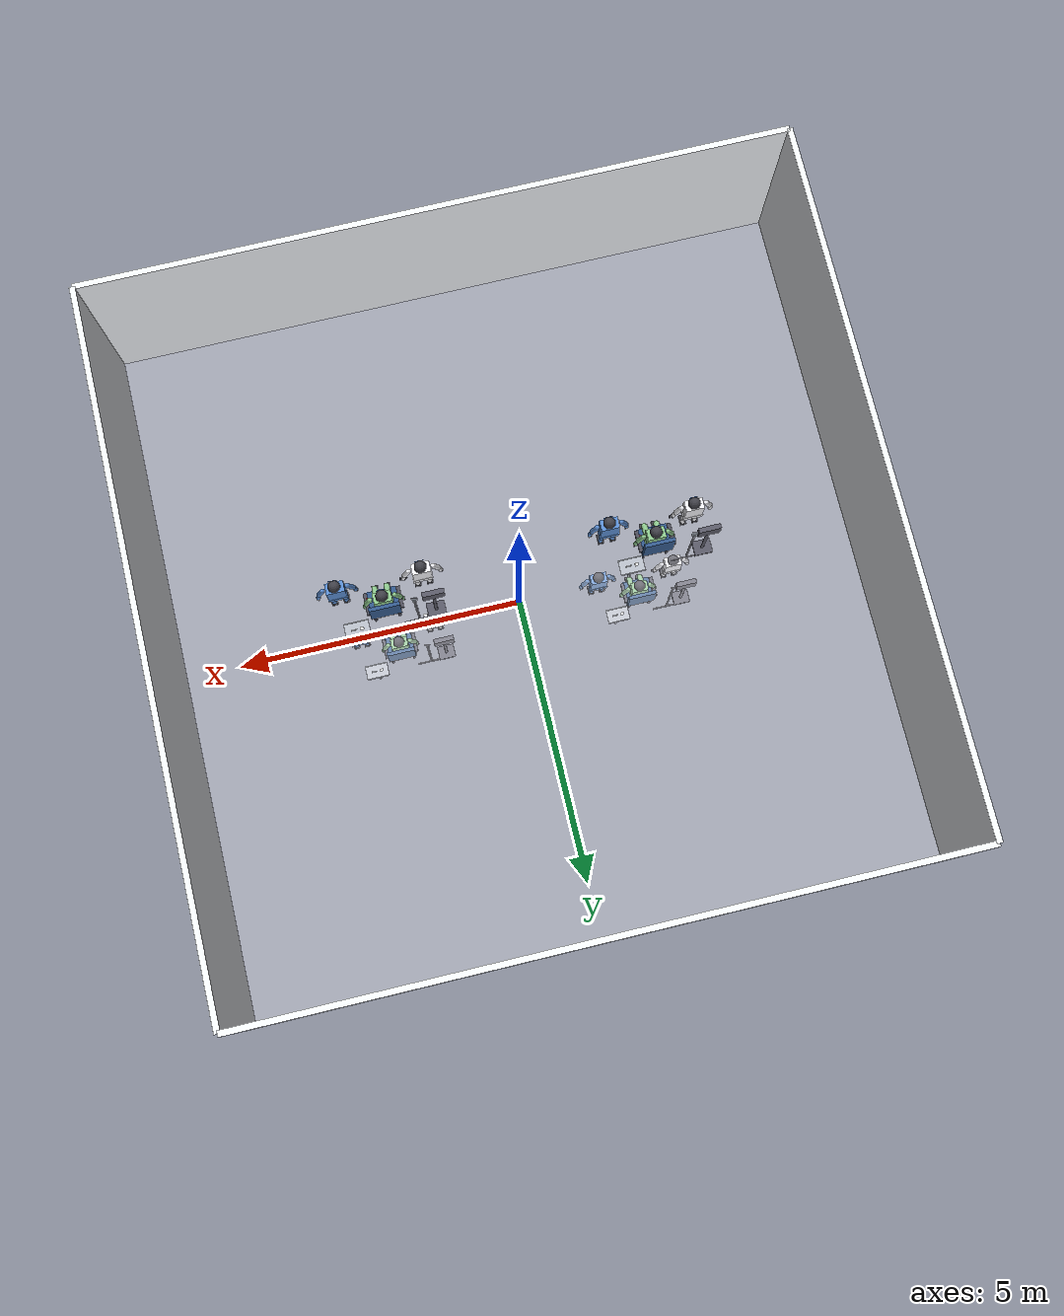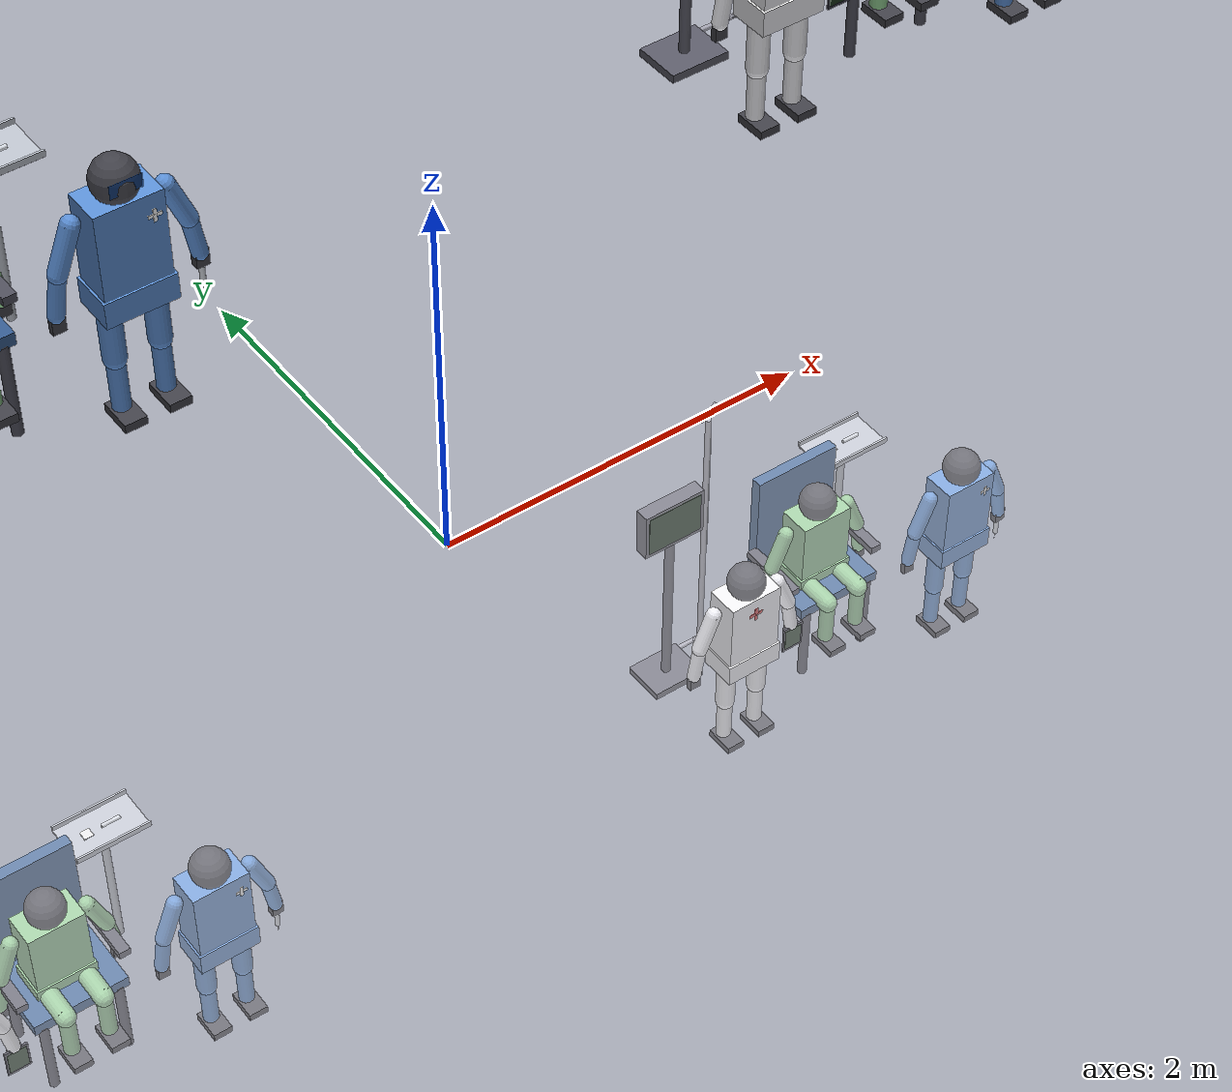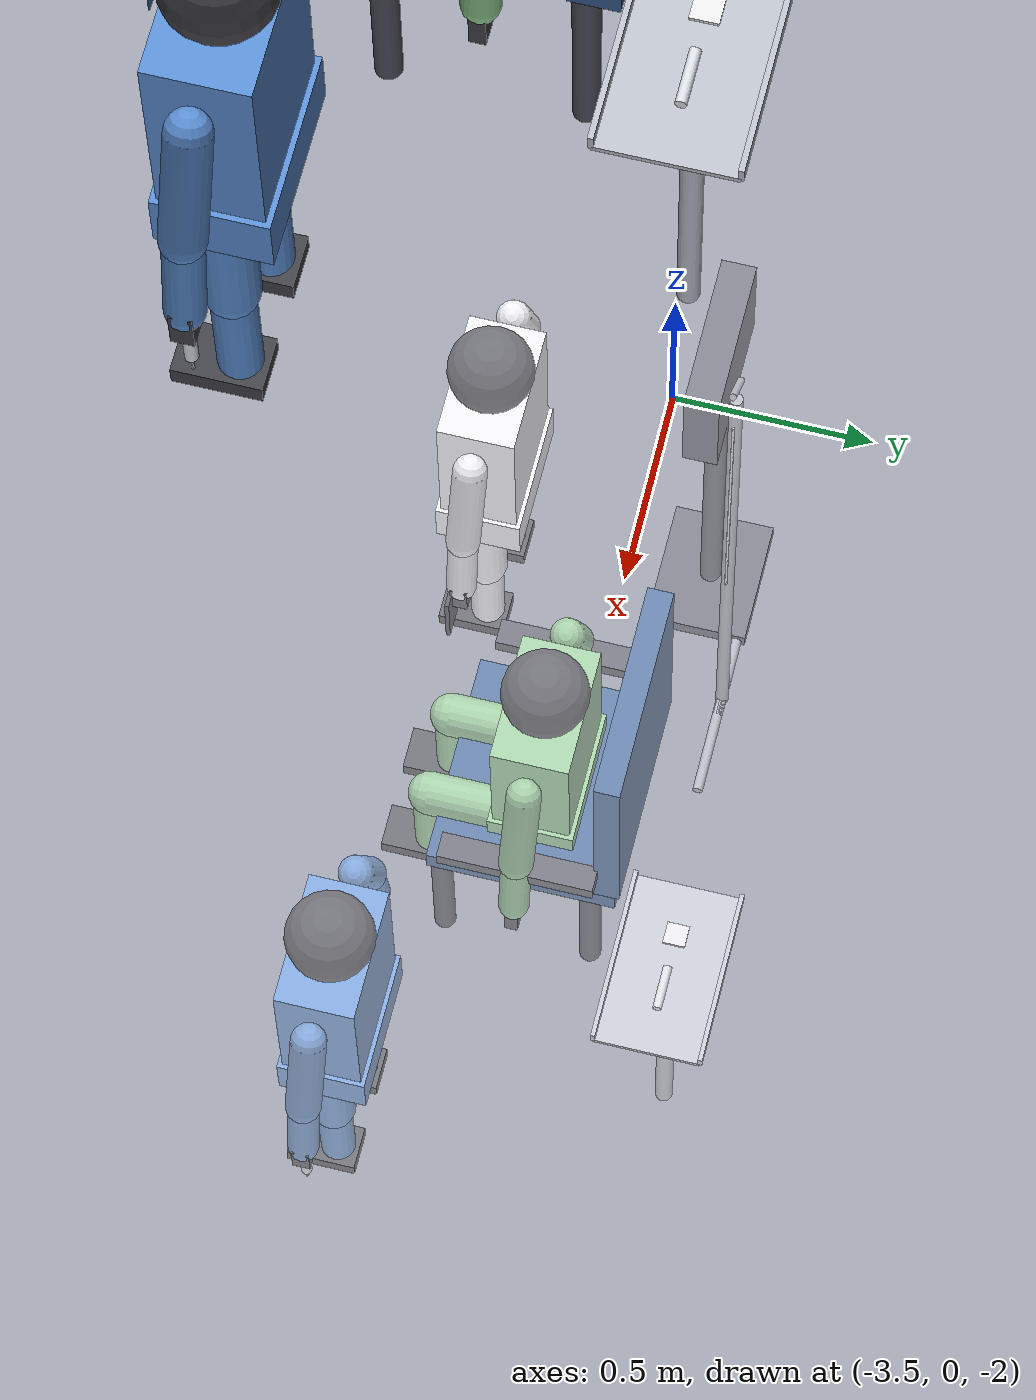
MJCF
<?xml version="1.0" encoding="utf-8"?>
<mujoco model="clinical_competition_4station">
  <compiler angle="degree" coordinate="local"/>

  <option gravity="0 0 -9.81" timestep="0.002">
    <flag warmstart="enable"/>
  </option>

  <default>
    <joint armature="0.01" damping="0.5" limited="true"/>
    <geom condim="3" friction="1.0 0.5 0.5" margin="0.001"/>
  </default>

  <asset>
    <!-- Environment Materials -->
    <material name="floor_tile" rgba="0.92 0.92 0.95 1" specular="0.3"/>
    <material name="wall" rgba="0.95 0.96 0.98 1"/>
    <material name="ceiling" rgba="0.98 0.98 1.0 1"/>

    <!-- Role-Based Robot Materials -->
    <material name="doctor_shell" rgba="0.95 0.95 0.97 1" specular="0.4"/>
    <material name="nurse_shell" rgba="0.35 0.55 0.82 1" specular="0.3"/>
    <material name="patient_gown" rgba="0.55 0.78 0.55 1" specular="0.1"/>
    <material name="robot_joint" rgba="0.25 0.25 0.28 1" specular="0.6"/>
    <material name="robot_visor" rgba="0.1 0.3 0.6 0.8" specular="0.8"/>

    <!-- Medical Equipment Materials -->
    <material name="chair_frame" rgba="0.3 0.3 0.35 1" specular="0.5"/>
    <material name="chair_cushion" rgba="0.2 0.35 0.55 1" specular="0.1"/>
    <material name="syringe_body" rgba="0.85 0.87 0.9 1" specular="0.7"/>
    <material name="syringe_plunger" rgba="0.4 0.4 0.45 1"/>
    <material name="needle" rgba="0.75 0.77 0.8 1" specular="0.9"/>
    <material name="tray_metal" rgba="0.72 0.74 0.78 1" specular="0.8"/>
    <material name="iv_stand" rgba="0.65 0.65 0.7 1" specular="0.6"/>
    <material name="iv_bag" rgba="0.8 0.85 0.9 0.7"/>
    <material name="monitor_screen" rgba="0.05 0.15 0.05 1" specular="0.2"/>
    <material name="monitor_body" rgba="0.35 0.35 0.4 1"/>
    <material name="tablet_body" rgba="0.2 0.2 0.25 1" specular="0.5"/>
    <material name="tablet_screen" rgba="0.1 0.2 0.1 1" specular="0.3"/>
  </asset>

  <worldbody>
    <!-- ENVIRONMENT: Larger Hospital Room (~12x12m) -->
    <geom name="floor" type="plane" size="6 6 0.05" material="floor_tile"/>

    <!-- Overhead lighting (4 lights for even coverage) -->
    <light name="overhead_1" pos="-2.25 -2.0 3.5" dir="0 0 -1" diffuse="0.8 0.8 0.85"
           specular="0.3 0.3 0.3" castshadow="true"/>
    <light name="overhead_2" pos="2.25 -2.0 3.5" dir="0 0 -1" diffuse="0.8 0.8 0.85"
           specular="0.3 0.3 0.3" castshadow="true"/>
    <light name="overhead_3" pos="-2.25 2.0 3.5" dir="0 0 -1" diffuse="0.8 0.8 0.85"
           specular="0.3 0.3 0.3" castshadow="true"/>
    <light name="overhead_4" pos="2.25 2.0 3.5" dir="0 0 -1" diffuse="0.8 0.8 0.85"
           specular="0.3 0.3 0.3" castshadow="true"/>
    <light name="fill_light" pos="0 -5 3.0" dir="0 0.5 -0.7" diffuse="0.3 0.3 0.35"/>

    <!-- Hospital Room Walls -->
    <geom name="wall_back" type="box" size="6 0.05 1.8" pos="0 -6 1.8" material="wall"/>
    <geom name="wall_front" type="box" size="6 0.05 1.8" pos="0 6 1.8" material="wall"/>
    <geom name="wall_left" type="box" size="0.05 6 1.8" pos="-6 0 1.8" material="wall"/>
    <geom name="wall_right" type="box" size="0.05 6 1.8" pos="6 0 1.8" material="wall"/>

    <!-- STATION A: center=(-2.25, 0, -2.0)                   -->
    <!-- Doctor LEFT, Patient CENTER (seated), Nurse RIGHT (syringe)  -->
    <!-- All facing -Y                                                 -->

    <!-- ======== STATION A: Examination Chair ======== -->
    <body name="station_a_exam_chair" pos="-2.25 0 -2">
      <geom name="station_a_chair_leg_fl" type="cylinder" size="0.025" fromto="-0.2 -0.2 0 -0.2 -0.2 0.45"
            material="chair_frame"/>
      <geom name="station_a_chair_leg_fr" type="cylinder" size="0.025" fromto="0.2 -0.2 0 0.2 -0.2 0.45"
            material="chair_frame"/>
      <geom name="station_a_chair_leg_bl" type="cylinder" size="0.025" fromto="-0.2 0.15 0 -0.2 0.15 0.45"
            material="chair_frame"/>
      <geom name="station_a_chair_leg_br" type="cylinder" size="0.025" fromto="0.2 0.15 0 0.2 0.15 0.45"
            material="chair_frame"/>
      <geom name="station_a_chair_seat" type="box" size="0.25 0.22 0.03" pos="0 0 0.47"
            material="chair_cushion"/>
      <geom name="station_a_chair_back" type="box" size="0.25 0.03 0.3" pos="0 0.2 0.8"
            material="chair_cushion"/>
      <geom name="station_a_armrest_r" type="box" size="0.03 0.18 0.02" pos="0.27 0 0.62"
            material="chair_frame"/>
      <geom name="station_a_armrest_l" type="box" size="0.03 0.18 0.02" pos="-0.27 0 0.62"
            material="chair_frame"/>
    </body>

    <!-- ======== STATION A: Patient (Seated G1 Humanoid) ======== -->
    <body name="station_a_patient_root" pos="-2.25 0 -1.5">
      <!-- Pelvis -->
      <geom name="station_a_patient_pelvis" type="box" size="0.16 0.1 0.06" pos="0 0 0"
            material="patient_gown"/>

      <!-- Torso -->
      <body name="station_a_patient_torso" pos="0 0 0.06">
        <geom name="station_a_patient_torso_geom" type="box" size="0.15 0.09 0.18"
              pos="0 0 0.18" material="patient_gown"/>

        <!-- Head -->
        <body name="station_a_patient_head" pos="0 0 0.42">
          <geom name="station_a_patient_head_geom" type="sphere" size="0.1" material="robot_joint"/>
          <geom name="station_a_patient_visor" type="box" size="0.07 0.001 0.03" pos="0 -0.09 0.02"
                material="robot_visor"/>
        </body>

        <!-- Right Upper Arm (INJECTION SITE on right deltoid, closest to nurse) -->
        <body name="station_a_patient_r_shoulder" pos="0.2 0 0.3">
          <joint name="station_a_patient_r_shoulder_pitch" type="hinge" axis="1 0 0"
                 range="-90 90" pos="0 0 0"/>
          <geom name="station_a_patient_r_upper_arm" type="capsule" size="0.04"
                fromto="0 0 0 0.08 0 -0.2" material="patient_gown"/>

          <!-- Deltoid injection target site -->
          <site name="station_a_injection_target" pos="0.04 -0.04 -0.08" size="0.025"
                rgba="1 0.2 0.2 0.5"/>

          <!-- Right Forearm -->
          <body name="station_a_patient_r_elbow" pos="0.08 0 -0.2">
            <joint name="station_a_patient_r_elbow_flex" type="hinge" axis="1 0 0"
                   range="0 130" pos="0 0 0"/>
            <geom name="station_a_patient_r_forearm" type="capsule" size="0.035"
                  fromto="0 0 0 0.03 0 -0.18" material="patient_gown"/>
            <geom name="station_a_patient_r_hand" type="box" size="0.03 0.015 0.04"
                  pos="0.03 0 -0.22" material="robot_joint"/>
          </body>
        </body>

        <!-- Left Upper Arm -->
        <body name="station_a_patient_l_shoulder" pos="-0.2 0 0.3">
          <joint name="station_a_patient_l_shoulder_pitch" type="hinge" axis="1 0 0"
                 range="-90 90" pos="0 0 0"/>
          <geom name="station_a_patient_l_upper_arm" type="capsule" size="0.04"
                fromto="0 0 0 -0.08 0 -0.2" material="patient_gown"/>
          <body name="station_a_patient_l_elbow" pos="-0.08 0 -0.2">
            <joint name="station_a_patient_l_elbow_flex" type="hinge" axis="1 0 0"
                   range="0 130" pos="0 0 0"/>
            <geom name="station_a_patient_l_forearm" type="capsule" size="0.035"
                  fromto="0 0 0 -0.03 0 -0.18" material="patient_gown"/>
            <geom name="station_a_patient_l_hand" type="box" size="0.03 0.015 0.04"
                  pos="-0.03 0 -0.22" material="robot_joint"/>
          </body>
        </body>
      </body>

      <!-- Right Thigh (seated, horizontal) -->
      <body name="station_a_patient_r_hip" pos="0.1 0 0">
        <joint name="station_a_patient_r_hip_flex" type="hinge" axis="1 0 0"
               range="-120 30" pos="0 0 0"/>
        <geom name="station_a_patient_r_thigh" type="capsule" size="0.05"
              fromto="0 0 0 0 -0.25 0" material="patient_gown"/>
        <body name="station_a_patient_r_knee" pos="0 -0.25 0">
          <joint name="station_a_patient_r_knee_flex" type="hinge" axis="1 0 0"
                 range="-130 0" pos="0 0 0"/>
          <geom name="station_a_patient_r_shin" type="capsule" size="0.04"
                fromto="0 0 0 0 0 -0.25" material="patient_gown"/>
          <geom name="station_a_patient_r_foot" type="box" size="0.05 0.08 0.02"
                pos="0 -0.03 -0.27" material="robot_joint"/>
        </body>
      </body>

      <!-- Left Thigh (seated, horizontal) -->
      <body name="station_a_patient_l_hip" pos="-0.1 0 0">
        <joint name="station_a_patient_l_hip_flex" type="hinge" axis="1 0 0"
               range="-120 30" pos="0 0 0"/>
        <geom name="station_a_patient_l_thigh" type="capsule" size="0.05"
              fromto="0 0 0 0 -0.25 0" material="patient_gown"/>
        <body name="station_a_patient_l_knee" pos="0 -0.25 0">
          <joint name="station_a_patient_l_knee_flex" type="hinge" axis="1 0 0"
                 range="-130 0" pos="0 0 0"/>
          <geom name="station_a_patient_l_shin" type="capsule" size="0.04"
                fromto="0 0 0 0 0 -0.25" material="patient_gown"/>
          <geom name="station_a_patient_l_foot" type="box" size="0.05 0.08 0.02"
                pos="0 -0.03 -0.27" material="robot_joint"/>
        </body>
      </body>
    </body>

    <!-- ======== STATION A: Doctor (Standing G1 Humanoid, LEFT of patient) ======== -->
    <!-- Doctor holds tablet (not syringe), white shell material -->
    <body name="station_a_doctor_root" pos="-2.95 -0.3 -2">
      <!-- Pelvis -->
      <geom name="station_a_doctor_pelvis" type="box" size="0.16 0.1 0.06" pos="0 0 0.55"
            material="doctor_shell"/>

      <!-- Torso -->
      <body name="station_a_doctor_torso" pos="0 0 0.61">
        <geom name="station_a_doctor_torso_geom" type="box" size="0.15 0.09 0.2"
              pos="0 0 0.2" material="doctor_shell"/>
        <!-- Medical cross emblem -->
        <geom name="station_a_doctor_cross_h" type="box" size="0.04 0.001 0.01"
              pos="0 -0.091 0.3" rgba="0.8 0.15 0.15 1"/>
        <geom name="station_a_doctor_cross_v" type="box" size="0.01 0.001 0.04"
              pos="0 -0.091 0.3" rgba="0.8 0.15 0.15 1"/>

        <!-- Head -->
        <body name="station_a_doctor_head" pos="0 0 0.46">
          <geom name="station_a_doctor_head_geom" type="sphere" size="0.1" material="robot_joint"/>
          <geom name="station_a_doctor_visor" type="box" size="0.07 0.001 0.03" pos="0 -0.09 0.02"
                material="robot_visor"/>
        </body>

        <!-- Right Arm (holds tablet for charting/gesturing) -->
        <body name="station_a_doctor_r_shoulder" pos="0.2 0 0.34">
          <joint name="station_a_doctor_r_shoulder_pitch" type="hinge" axis="1 0 0"
                 range="-180 90" pos="0 0 0"/>
          <geom name="station_a_doctor_r_upper_arm" type="capsule" size="0.04"
                fromto="0 0 0 0.08 0 -0.2" material="doctor_shell"/>
          <body name="station_a_doctor_r_elbow" pos="0.08 0 -0.2">
            <joint name="station_a_doctor_r_elbow_flex" type="hinge" axis="1 0 0"
                   range="0 140" pos="0 0 0"/>
            <geom name="station_a_doctor_r_forearm" type="capsule" size="0.035"
                  fromto="0 0 0 0.03 0 -0.18" material="doctor_shell"/>
            <!-- Hand holding tablet -->
            <body name="station_a_doctor_r_hand" pos="0.03 0 -0.2">
              <geom name="station_a_doctor_hand_geom" type="box" size="0.03 0.02 0.04"
                    material="robot_joint"/>
              <!-- Tablet/clipboard -->
              <geom name="station_a_doctor_tablet" type="box" size="0.06 0.005 0.08"
                    pos="0 -0.02 -0.06" material="tablet_body"/>
              <geom name="station_a_doctor_tablet_screen" type="box" size="0.05 0.001 0.065"
                    pos="0 -0.026 -0.06" material="tablet_screen"/>
            </body>
          </body>
        </body>

        <!-- Left Arm -->
        <body name="station_a_doctor_l_shoulder" pos="-0.2 0 0.34">
          <joint name="station_a_doctor_l_shoulder_pitch" type="hinge" axis="1 0 0"
                 range="-180 90" pos="0 0 0"/>
          <geom name="station_a_doctor_l_upper_arm" type="capsule" size="0.04"
                fromto="0 0 0 -0.08 0 -0.2" material="doctor_shell"/>
          <body name="station_a_doctor_l_elbow" pos="-0.08 0 -0.2">
            <joint name="station_a_doctor_l_elbow_flex" type="hinge" axis="1 0 0"
                   range="0 140" pos="0 0 0"/>
            <geom name="station_a_doctor_l_forearm" type="capsule" size="0.035"
                  fromto="0 0 0 -0.03 0 -0.18" material="doctor_shell"/>
            <geom name="station_a_doctor_l_hand" type="box" size="0.03 0.015 0.04"
                  pos="-0.03 0 -0.22" material="robot_joint"/>
          </body>
        </body>
      </body>

      <!-- Right Leg -->
      <body name="station_a_doctor_r_hip" pos="0.1 0 0.5">
        <joint name="station_a_doctor_r_hip_flex" type="hinge" axis="1 0 0"
               range="-30 90" pos="0 0 0"/>
        <geom name="station_a_doctor_r_thigh" type="capsule" size="0.05"
              fromto="0 0 0 0 0 -0.25" material="doctor_shell"/>
        <body name="station_a_doctor_r_knee" pos="0 0 -0.25">
          <joint name="station_a_doctor_r_knee_flex" type="hinge" axis="1 0 0"
                 range="0 130" pos="0 0 0"/>
          <geom name="station_a_doctor_r_shin" type="capsule" size="0.04"
                fromto="0 0 0 0 0 -0.25" material="doctor_shell"/>
          <geom name="station_a_doctor_r_foot" type="box" size="0.05 0.08 0.02"
                pos="0 -0.03 -0.27" material="robot_joint"/>
        </body>
      </body>

      <!-- Left Leg -->
      <body name="station_a_doctor_l_hip" pos="-0.1 0 0.5">
        <joint name="station_a_doctor_l_hip_flex" type="hinge" axis="1 0 0"
               range="-30 90" pos="0 0 0"/>
        <geom name="station_a_doctor_l_thigh" type="capsule" size="0.05"
              fromto="0 0 0 0 0 -0.25" material="doctor_shell"/>
        <body name="station_a_doctor_l_knee" pos="0 0 -0.25">
          <joint name="station_a_doctor_l_knee_flex" type="hinge" axis="1 0 0"
                 range="0 130" pos="0 0 0"/>
          <geom name="station_a_doctor_l_shin" type="capsule" size="0.04"
                fromto="0 0 0 0 0 -0.25" material="doctor_shell"/>
          <geom name="station_a_doctor_l_foot" type="box" size="0.05 0.08 0.02"
                pos="0 -0.03 -0.27" material="robot_joint"/>
        </body>
      </body>
    </body>

    <!-- ======== STATION A: Nurse (Standing G1 Humanoid, RIGHT of patient) ======== -->
    <!-- Nurse holds syringe with needle_tip site, blue shell material -->
    <body name="station_a_nurse_root" pos="-1.55 -0.3 -2">
      <!-- Pelvis -->
      <geom name="station_a_nurse_pelvis" type="box" size="0.16 0.1 0.06" pos="0 0 0.55"
            material="nurse_shell"/>

      <!-- Torso -->
      <body name="station_a_nurse_torso" pos="0 0 0.61">
        <geom name="station_a_nurse_torso_geom" type="box" size="0.15 0.09 0.2"
              pos="0 0 0.2" material="nurse_shell"/>
        <!-- Medical plus badge -->
        <geom name="station_a_nurse_badge_h" type="box" size="0.03 0.001 0.008"
              pos="0.1 -0.091 0.3" rgba="1 1 1 1"/>
        <geom name="station_a_nurse_badge_v" type="box" size="0.008 0.001 0.03"
              pos="0.1 -0.091 0.3" rgba="1 1 1 1"/>

        <!-- Head -->
        <body name="station_a_nurse_head" pos="0 0 0.46">
          <geom name="station_a_nurse_head_geom" type="sphere" size="0.1" material="robot_joint"/>
          <geom name="station_a_nurse_visor" type="box" size="0.07 0.001 0.03" pos="0 -0.09 0.02"
                material="robot_visor"/>
        </body>

        <!-- Right Arm (holds syringe for injection) -->
        <body name="station_a_nurse_r_shoulder" pos="0.2 0 0.34">
          <joint name="station_a_nurse_r_shoulder_pitch" type="hinge" axis="1 0 0"
                 range="-180 90" pos="0 0 0"/>
          <joint name="station_a_nurse_r_shoulder_yaw" type="hinge" axis="0 0 1"
                 range="-90 90" pos="0 0 0"/>
          <geom name="station_a_nurse_r_upper_arm" type="capsule" size="0.04"
                fromto="0 0 0 0.08 0 -0.2" material="nurse_shell"/>
          <body name="station_a_nurse_r_elbow" pos="0.08 0 -0.2">
            <joint name="station_a_nurse_r_elbow_flex" type="hinge" axis="1 0 0"
                   range="0 140" pos="0 0 0"/>
            <geom name="station_a_nurse_r_forearm" type="capsule" size="0.035"
                  fromto="0 0 0 0.03 0 -0.18" material="nurse_shell"/>

            <!-- Hand holding syringe -->
            <body name="station_a_nurse_r_hand" pos="0.03 0 -0.2">
              <joint name="station_a_nurse_r_wrist" type="hinge" axis="0 1 0"
                     range="-45 45" pos="0 0 0"/>
              <geom name="station_a_nurse_hand_geom" type="box" size="0.03 0.02 0.04"
                    material="robot_joint"/>
              <!-- Syringe -->
              <geom name="station_a_syringe_barrel" type="cylinder" size="0.012 0.06"
                    pos="0 0 -0.08" material="syringe_body"/>
              <geom name="station_a_syringe_plunger" type="cylinder" size="0.008 0.03"
                    pos="0 0 -0.02" material="syringe_plunger"/>
              <geom name="station_a_syringe_needle" type="cylinder" size="0.002 0.025"
                    pos="0 0 -0.155" material="needle"/>
              <!-- Needle tip site for contact detection -->
              <site name="station_a_needle_tip" pos="0 0 -0.18" size="0.003"
                    rgba="0.8 0.8 0.85 1"/>
            </body>
          </body>
        </body>

        <!-- Left Arm -->
        <body name="station_a_nurse_l_shoulder" pos="-0.2 0 0.34">
          <joint name="station_a_nurse_l_shoulder_pitch" type="hinge" axis="1 0 0"
                 range="-180 90" pos="0 0 0"/>
          <geom name="station_a_nurse_l_upper_arm" type="capsule" size="0.04"
                fromto="0 0 0 -0.08 0 -0.2" material="nurse_shell"/>
          <body name="station_a_nurse_l_elbow" pos="-0.08 0 -0.2">
            <joint name="station_a_nurse_l_elbow_flex" type="hinge" axis="1 0 0"
                   range="0 140" pos="0 0 0"/>
            <geom name="station_a_nurse_l_forearm" type="capsule" size="0.035"
                  fromto="0 0 0 -0.03 0 -0.18" material="nurse_shell"/>
            <geom name="station_a_nurse_l_hand" type="box" size="0.03 0.015 0.04"
                  pos="-0.03 0 -0.22" material="robot_joint"/>
          </body>
        </body>
      </body>

      <!-- Right Leg -->
      <body name="station_a_nurse_r_hip" pos="0.1 0 0.5">
        <joint name="station_a_nurse_r_hip_flex" type="hinge" axis="1 0 0"
               range="-30 90" pos="0 0 0"/>
        <geom name="station_a_nurse_r_thigh" type="capsule" size="0.05"
              fromto="0 0 0 0 0 -0.25" material="nurse_shell"/>
        <body name="station_a_nurse_r_knee" pos="0 0 -0.25">
          <joint name="station_a_nurse_r_knee_flex" type="hinge" axis="1 0 0"
                 range="0 130" pos="0 0 0"/>
          <geom name="station_a_nurse_r_shin" type="capsule" size="0.04"
                fromto="0 0 0 0 0 -0.25" material="nurse_shell"/>
          <geom name="station_a_nurse_r_foot" type="box" size="0.05 0.08 0.02"
                pos="0 -0.03 -0.27" material="robot_joint"/>
        </body>
      </body>

      <!-- Left Leg -->
      <body name="station_a_nurse_l_hip" pos="-0.1 0 0.5">
        <joint name="station_a_nurse_l_hip_flex" type="hinge" axis="1 0 0"
               range="-30 90" pos="0 0 0"/>
        <geom name="station_a_nurse_l_thigh" type="capsule" size="0.05"
              fromto="0 0 0 0 0 -0.25" material="nurse_shell"/>
        <body name="station_a_nurse_l_knee" pos="0 0 -0.25">
          <joint name="station_a_nurse_l_knee_flex" type="hinge" axis="1 0 0"
                 range="0 130" pos="0 0 0"/>
          <geom name="station_a_nurse_l_shin" type="capsule" size="0.04"
                fromto="0 0 0 0 0 -0.25" material="nurse_shell"/>
          <geom name="station_a_nurse_l_foot" type="box" size="0.05 0.08 0.02"
                pos="0 -0.03 -0.27" material="robot_joint"/>
        </body>
      </body>
    </body>

    <!-- ======== STATION A: Medical Equipment ======== -->

    <!-- IV Stand (behind patient, left side) -->
    <body name="station_a_iv_stand" pos="-2.75 0.3 -2">
      <geom name="station_a_iv_pole" type="cylinder" size="0.015 0.8" pos="0 0 0.8"
            material="iv_stand"/>
      <geom name="station_a_iv_base_1" type="cylinder" size="0.012 0.15" pos="0.1 0 0.015"
            euler="0 90 0" material="iv_stand"/>
      <geom name="station_a_iv_base_2" type="cylinder" size="0.012 0.15" pos="-0.1 0 0.015"
            euler="0 90 0" material="iv_stand"/>
      <geom name="station_a_iv_hook" type="cylinder" size="0.008 0.06" pos="0 0 1.65"
            euler="0 45 0" material="iv_stand"/>
      <geom name="station_a_iv_bag" type="box" size="0.04 0.02 0.07" pos="0 0 1.55"
            material="iv_bag"/>
      <geom name="station_a_iv_tube" type="cylinder" size="0.003 0.4" pos="0.02 0 1.1"
            material="syringe_body"/>
    </body>

    <!-- Medical Instrument Tray (behind patient, right side) -->
    <body name="station_a_med_tray" pos="-1.75 0.4 -2">
      <geom name="station_a_tray_leg" type="cylinder" size="0.02 0.4" pos="0 0 0.4"
            material="tray_metal"/>
      <geom name="station_a_tray_surface" type="box" size="0.2 0.12 0.005" pos="0 0 0.8"
            material="tray_metal"/>
      <geom name="station_a_tray_rim_f" type="box" size="0.2 0.005 0.015" pos="0 -0.12 0.815"
            material="tray_metal"/>
      <geom name="station_a_tray_rim_b" type="box" size="0.2 0.005 0.015" pos="0 0.12 0.815"
            material="tray_metal"/>
      <geom name="station_a_spare_syringe" type="cylinder" size="0.01 0.05" pos="0.05 0 0.815"
            euler="0 90 0" material="syringe_body"/>
      <geom name="station_a_swab_packet" type="box" size="0.025 0.025 0.003" pos="-0.08 0 0.81"
            rgba="0.9 0.9 0.9 1"/>
    </body>

    <!-- Vital Signs Monitor (behind patient, far left) -->
    <body name="station_a_vitals_monitor" pos="-3.05 0.2 -2">
      <geom name="station_a_monitor_stand" type="cylinder" size="0.025 0.5" pos="0 0 0.5"
            material="monitor_body"/>
      <geom name="station_a_monitor_base" type="box" size="0.15 0.12 0.02" pos="0 0 0.02"
            material="monitor_body"/>
      <geom name="station_a_monitor_housing" type="box" size="0.18 0.04 0.14" pos="0 0 1.15"
            material="monitor_body"/>
      <geom name="station_a_monitor_display" type="box" size="0.16 0.001 0.12" pos="0 -0.041 1.15"
            material="monitor_screen"/>
    </body>

    <!-- STATION B: center=(2.25, 0, -2.0)                   -->
    <!-- Doctor LEFT, Patient CENTER (seated), Nurse RIGHT (syringe)  -->
    <!-- All facing -Y                                                 -->

    <!-- ======== STATION B: Examination Chair ======== -->
    <body name="station_b_exam_chair" pos="2.25 0 -2">
      <geom name="station_b_chair_leg_fl" type="cylinder" size="0.025" fromto="-0.2 -0.2 0 -0.2 -0.2 0.45"
            material="chair_frame"/>
      <geom name="station_b_chair_leg_fr" type="cylinder" size="0.025" fromto="0.2 -0.2 0 0.2 -0.2 0.45"
            material="chair_frame"/>
      <geom name="station_b_chair_leg_bl" type="cylinder" size="0.025" fromto="-0.2 0.15 0 -0.2 0.15 0.45"
            material="chair_frame"/>
      <geom name="station_b_chair_leg_br" type="cylinder" size="0.025" fromto="0.2 0.15 0 0.2 0.15 0.45"
            material="chair_frame"/>
      <geom name="station_b_chair_seat" type="box" size="0.25 0.22 0.03" pos="0 0 0.47"
            material="chair_cushion"/>
      <geom name="station_b_chair_back" type="box" size="0.25 0.03 0.3" pos="0 0.2 0.8"
            material="chair_cushion"/>
      <geom name="station_b_armrest_r" type="box" size="0.03 0.18 0.02" pos="0.27 0 0.62"
            material="chair_frame"/>
      <geom name="station_b_armrest_l" type="box" size="0.03 0.18 0.02" pos="-0.27 0 0.62"
            material="chair_frame"/>
    </body>

    <!-- ======== STATION B: Patient (Seated G1 Humanoid) ======== -->
    <body name="station_b_patient_root" pos="2.25 0 -1.5">
      <!-- Pelvis -->
      <geom name="station_b_patient_pelvis" type="box" size="0.16 0.1 0.06" pos="0 0 0"
            material="patient_gown"/>

      <!-- Torso -->
      <body name="station_b_patient_torso" pos="0 0 0.06">
        <geom name="station_b_patient_torso_geom" type="box" size="0.15 0.09 0.18"
              pos="0 0 0.18" material="patient_gown"/>

        <!-- Head -->
        <body name="station_b_patient_head" pos="0 0 0.42">
          <geom name="station_b_patient_head_geom" type="sphere" size="0.1" material="robot_joint"/>
          <geom name="station_b_patient_visor" type="box" size="0.07 0.001 0.03" pos="0 -0.09 0.02"
                material="robot_visor"/>
        </body>

        <!-- Right Upper Arm (INJECTION SITE on right deltoid, closest to nurse) -->
        <body name="station_b_patient_r_shoulder" pos="0.2 0 0.3">
          <joint name="station_b_patient_r_shoulder_pitch" type="hinge" axis="1 0 0"
                 range="-90 90" pos="0 0 0"/>
          <geom name="station_b_patient_r_upper_arm" type="capsule" size="0.04"
                fromto="0 0 0 0.08 0 -0.2" material="patient_gown"/>

          <!-- Deltoid injection target site -->
          <site name="station_b_injection_target" pos="0.04 -0.04 -0.08" size="0.025"
                rgba="1 0.2 0.2 0.5"/>

          <!-- Right Forearm -->
          <body name="station_b_patient_r_elbow" pos="0.08 0 -0.2">
            <joint name="station_b_patient_r_elbow_flex" type="hinge" axis="1 0 0"
                   range="0 130" pos="0 0 0"/>
            <geom name="station_b_patient_r_forearm" type="capsule" size="0.035"
                  fromto="0 0 0 0.03 0 -0.18" material="patient_gown"/>
            <geom name="station_b_patient_r_hand" type="box" size="0.03 0.015 0.04"
                  pos="0.03 0 -0.22" material="robot_joint"/>
          </body>
        </body>

        <!-- Left Upper Arm -->
        <body name="station_b_patient_l_shoulder" pos="-0.2 0 0.3">
          <joint name="station_b_patient_l_shoulder_pitch" type="hinge" axis="1 0 0"
                 range="-90 90" pos="0 0 0"/>
          <geom name="station_b_patient_l_upper_arm" type="capsule" size="0.04"
                fromto="0 0 0 -0.08 0 -0.2" material="patient_gown"/>
          <body name="station_b_patient_l_elbow" pos="-0.08 0 -0.2">
            <joint name="station_b_patient_l_elbow_flex" type="hinge" axis="1 0 0"
                   range="0 130" pos="0 0 0"/>
            <geom name="station_b_patient_l_forearm" type="capsule" size="0.035"
                  fromto="0 0 0 -0.03 0 -0.18" material="patient_gown"/>
            <geom name="station_b_patient_l_hand" type="box" size="0.03 0.015 0.04"
                  pos="-0.03 0 -0.22" material="robot_joint"/>
          </body>
        </body>
      </body>

      <!-- Right Thigh (seated, horizontal) -->
      <body name="station_b_patient_r_hip" pos="0.1 0 0">
        <joint name="station_b_patient_r_hip_flex" type="hinge" axis="1 0 0"
               range="-120 30" pos="0 0 0"/>
        <geom name="station_b_patient_r_thigh" type="capsule" size="0.05"
              fromto="0 0 0 0 -0.25 0" material="patient_gown"/>
        <body name="station_b_patient_r_knee" pos="0 -0.25 0">
          <joint name="station_b_patient_r_knee_flex" type="hinge" axis="1 0 0"
                 range="-130 0" pos="0 0 0"/>
          <geom name="station_b_patient_r_shin" type="capsule" size="0.04"
                fromto="0 0 0 0 0 -0.25" material="patient_gown"/>
          <geom name="station_b_patient_r_foot" type="box" size="0.05 0.08 0.02"
                pos="0 -0.03 -0.27" material="robot_joint"/>
        </body>
      </body>

      <!-- Left Thigh (seated, horizontal) -->
      <body name="station_b_patient_l_hip" pos="-0.1 0 0">
        <joint name="station_b_patient_l_hip_flex" type="hinge" axis="1 0 0"
               range="-120 30" pos="0 0 0"/>
        <geom name="station_b_patient_l_thigh" type="capsule" size="0.05"
              fromto="0 0 0 0 -0.25 0" material="patient_gown"/>
        <body name="station_b_patient_l_knee" pos="0 -0.25 0">
          <joint name="station_b_patient_l_knee_flex" type="hinge" axis="1 0 0"
                 range="-130 0" pos="0 0 0"/>
          <geom name="station_b_patient_l_shin" type="capsule" size="0.04"
                fromto="0 0 0 0 0 -0.25" material="patient_gown"/>
          <geom name="station_b_patient_l_foot" type="box" size="0.05 0.08 0.02"
                pos="0 -0.03 -0.27" material="robot_joint"/>
        </body>
      </body>
    </body>

    <!-- ======== STATION B: Doctor (Standing G1 Humanoid, LEFT of patient) ======== -->
    <!-- Doctor holds tablet (not syringe), white shell material -->
    <body name="station_b_doctor_root" pos="1.55 -0.3 -2">
      <!-- Pelvis -->
      <geom name="station_b_doctor_pelvis" type="box" size="0.16 0.1 0.06" pos="0 0 0.55"
            material="doctor_shell"/>

      <!-- Torso -->
      <body name="station_b_doctor_torso" pos="0 0 0.61">
        <geom name="station_b_doctor_torso_geom" type="box" size="0.15 0.09 0.2"
              pos="0 0 0.2" material="doctor_shell"/>
        <!-- Medical cross emblem -->
        <geom name="station_b_doctor_cross_h" type="box" size="0.04 0.001 0.01"
              pos="0 -0.091 0.3" rgba="0.8 0.15 0.15 1"/>
        <geom name="station_b_doctor_cross_v" type="box" size="0.01 0.001 0.04"
              pos="0 -0.091 0.3" rgba="0.8 0.15 0.15 1"/>

        <!-- Head -->
        <body name="station_b_doctor_head" pos="0 0 0.46">
          <geom name="station_b_doctor_head_geom" type="sphere" size="0.1" material="robot_joint"/>
          <geom name="station_b_doctor_visor" type="box" size="0.07 0.001 0.03" pos="0 -0.09 0.02"
                material="robot_visor"/>
        </body>

        <!-- Right Arm (holds tablet for charting/gesturing) -->
        <body name="station_b_doctor_r_shoulder" pos="0.2 0 0.34">
          <joint name="station_b_doctor_r_shoulder_pitch" type="hinge" axis="1 0 0"
                 range="-180 90" pos="0 0 0"/>
          <geom name="station_b_doctor_r_upper_arm" type="capsule" size="0.04"
                fromto="0 0 0 0.08 0 -0.2" material="doctor_shell"/>
          <body name="station_b_doctor_r_elbow" pos="0.08 0 -0.2">
            <joint name="station_b_doctor_r_elbow_flex" type="hinge" axis="1 0 0"
                   range="0 140" pos="0 0 0"/>
            <geom name="station_b_doctor_r_forearm" type="capsule" size="0.035"
                  fromto="0 0 0 0.03 0 -0.18" material="doctor_shell"/>
            <!-- Hand holding tablet -->
            <body name="station_b_doctor_r_hand" pos="0.03 0 -0.2">
              <geom name="station_b_doctor_hand_geom" type="box" size="0.03 0.02 0.04"
                    material="robot_joint"/>
              <!-- Tablet/clipboard -->
              <geom name="station_b_doctor_tablet" type="box" size="0.06 0.005 0.08"
                    pos="0 -0.02 -0.06" material="tablet_body"/>
              <geom name="station_b_doctor_tablet_screen" type="box" size="0.05 0.001 0.065"
                    pos="0 -0.026 -0.06" material="tablet_screen"/>
            </body>
          </body>
        </body>

        <!-- Left Arm -->
        <body name="station_b_doctor_l_shoulder" pos="-0.2 0 0.34">
          <joint name="station_b_doctor_l_shoulder_pitch" type="hinge" axis="1 0 0"
                 range="-180 90" pos="0 0 0"/>
          <geom name="station_b_doctor_l_upper_arm" type="capsule" size="0.04"
                fromto="0 0 0 -0.08 0 -0.2" material="doctor_shell"/>
          <body name="station_b_doctor_l_elbow" pos="-0.08 0 -0.2">
            <joint name="station_b_doctor_l_elbow_flex" type="hinge" axis="1 0 0"
                   range="0 140" pos="0 0 0"/>
            <geom name="station_b_doctor_l_forearm" type="capsule" size="0.035"
                  fromto="0 0 0 -0.03 0 -0.18" material="doctor_shell"/>
            <geom name="station_b_doctor_l_hand" type="box" size="0.03 0.015 0.04"
                  pos="-0.03 0 -0.22" material="robot_joint"/>
          </body>
        </body>
      </body>

      <!-- Right Leg -->
      <body name="station_b_doctor_r_hip" pos="0.1 0 0.5">
        <joint name="station_b_doctor_r_hip_flex" type="hinge" axis="1 0 0"
               range="-30 90" pos="0 0 0"/>
        <geom name="station_b_doctor_r_thigh" type="capsule" size="0.05"
              fromto="0 0 0 0 0 -0.25" material="doctor_shell"/>
        <body name="station_b_doctor_r_knee" pos="0 0 -0.25">
          <joint name="station_b_doctor_r_knee_flex" type="hinge" axis="1 0 0"
                 range="0 130" pos="0 0 0"/>
          <geom name="station_b_doctor_r_shin" type="capsule" size="0.04"
                fromto="0 0 0 0 0 -0.25" material="doctor_shell"/>
          <geom name="station_b_doctor_r_foot" type="box" size="0.05 0.08 0.02"
                pos="0 -0.03 -0.27" material="robot_joint"/>
        </body>
      </body>

      <!-- Left Leg -->
      <body name="station_b_doctor_l_hip" pos="-0.1 0 0.5">
        <joint name="station_b_doctor_l_hip_flex" type="hinge" axis="1 0 0"
               range="-30 90" pos="0 0 0"/>
        <geom name="station_b_doctor_l_thigh" type="capsule" size="0.05"
              fromto="0 0 0 0 0 -0.25" material="doctor_shell"/>
        <body name="station_b_doctor_l_knee" pos="0 0 -0.25">
          <joint name="station_b_doctor_l_knee_flex" type="hinge" axis="1 0 0"
                 range="0 130" pos="0 0 0"/>
          <geom name="station_b_doctor_l_shin" type="capsule" size="0.04"
                fromto="0 0 0 0 0 -0.25" material="doctor_shell"/>
          <geom name="station_b_doctor_l_foot" type="box" size="0.05 0.08 0.02"
                pos="0 -0.03 -0.27" material="robot_joint"/>
        </body>
      </body>
    </body>

    <!-- ======== STATION B: Nurse (Standing G1 Humanoid, RIGHT of patient) ======== -->
    <!-- Nurse holds syringe with needle_tip site, blue shell material -->
    <body name="station_b_nurse_root" pos="2.95 -0.3 -2">
      <!-- Pelvis -->
      <geom name="station_b_nurse_pelvis" type="box" size="0.16 0.1 0.06" pos="0 0 0.55"
            material="nurse_shell"/>

      <!-- Torso -->
      <body name="station_b_nurse_torso" pos="0 0 0.61">
        <geom name="station_b_nurse_torso_geom" type="box" size="0.15 0.09 0.2"
              pos="0 0 0.2" material="nurse_shell"/>
        <!-- Medical plus badge -->
        <geom name="station_b_nurse_badge_h" type="box" size="0.03 0.001 0.008"
              pos="0.1 -0.091 0.3" rgba="1 1 1 1"/>
        <geom name="station_b_nurse_badge_v" type="box" size="0.008 0.001 0.03"
              pos="0.1 -0.091 0.3" rgba="1 1 1 1"/>

        <!-- Head -->
        <body name="station_b_nurse_head" pos="0 0 0.46">
          <geom name="station_b_nurse_head_geom" type="sphere" size="0.1" material="robot_joint"/>
          <geom name="station_b_nurse_visor" type="box" size="0.07 0.001 0.03" pos="0 -0.09 0.02"
                material="robot_visor"/>
        </body>

        <!-- Right Arm (holds syringe for injection) -->
        <body name="station_b_nurse_r_shoulder" pos="0.2 0 0.34">
          <joint name="station_b_nurse_r_shoulder_pitch" type="hinge" axis="1 0 0"
                 range="-180 90" pos="0 0 0"/>
          <joint name="station_b_nurse_r_shoulder_yaw" type="hinge" axis="0 0 1"
                 range="-90 90" pos="0 0 0"/>
          <geom name="station_b_nurse_r_upper_arm" type="capsule" size="0.04"
                fromto="0 0 0 0.08 0 -0.2" material="nurse_shell"/>
          <body name="station_b_nurse_r_elbow" pos="0.08 0 -0.2">
            <joint name="station_b_nurse_r_elbow_flex" type="hinge" axis="1 0 0"
                   range="0 140" pos="0 0 0"/>
            <geom name="station_b_nurse_r_forearm" type="capsule" size="0.035"
                  fromto="0 0 0 0.03 0 -0.18" material="nurse_shell"/>

            <!-- Hand holding syringe -->
            <body name="station_b_nurse_r_hand" pos="0.03 0 -0.2">
              <joint name="station_b_nurse_r_wrist" type="hinge" axis="0 1 0"
                     range="-45 45" pos="0 0 0"/>
              <geom name="station_b_nurse_hand_geom" type="box" size="0.03 0.02 0.04"
                    material="robot_joint"/>
              <!-- Syringe -->
              <geom name="station_b_syringe_barrel" type="cylinder" size="0.012 0.06"
                    pos="0 0 -0.08" material="syringe_body"/>
              <geom name="station_b_syringe_plunger" type="cylinder" size="0.008 0.03"
                    pos="0 0 -0.02" material="syringe_plunger"/>
              <geom name="station_b_syringe_needle" type="cylinder" size="0.002 0.025"
                    pos="0 0 -0.155" material="needle"/>
              <!-- Needle tip site for contact detection -->
              <site name="station_b_needle_tip" pos="0 0 -0.18" size="0.003"
                    rgba="0.8 0.8 0.85 1"/>
            </body>
          </body>
        </body>

        <!-- Left Arm -->
        <body name="station_b_nurse_l_shoulder" pos="-0.2 0 0.34">
          <joint name="station_b_nurse_l_shoulder_pitch" type="hinge" axis="1 0 0"
                 range="-180 90" pos="0 0 0"/>
          <geom name="station_b_nurse_l_upper_arm" type="capsule" size="0.04"
                fromto="0 0 0 -0.08 0 -0.2" material="nurse_shell"/>
          <body name="station_b_nurse_l_elbow" pos="-0.08 0 -0.2">
            <joint name="station_b_nurse_l_elbow_flex" type="hinge" axis="1 0 0"
                   range="0 140" pos="0 0 0"/>
            <geom name="station_b_nurse_l_forearm" type="capsule" size="0.035"
                  fromto="0 0 0 -0.03 0 -0.18" material="nurse_shell"/>
            <geom name="station_b_nurse_l_hand" type="box" size="0.03 0.015 0.04"
                  pos="-0.03 0 -0.22" material="robot_joint"/>
          </body>
        </body>
      </body>

      <!-- Right Leg -->
      <body name="station_b_nurse_r_hip" pos="0.1 0 0.5">
        <joint name="station_b_nurse_r_hip_flex" type="hinge" axis="1 0 0"
               range="-30 90" pos="0 0 0"/>
        <geom name="station_b_nurse_r_thigh" type="capsule" size="0.05"
              fromto="0 0 0 0 0 -0.25" material="nurse_shell"/>
        <body name="station_b_nurse_r_knee" pos="0 0 -0.25">
          <joint name="station_b_nurse_r_knee_flex" type="hinge" axis="1 0 0"
                 range="0 130" pos="0 0 0"/>
          <geom name="station_b_nurse_r_shin" type="capsule" size="0.04"
                fromto="0 0 0 0 0 -0.25" material="nurse_shell"/>
          <geom name="station_b_nurse_r_foot" type="box" size="0.05 0.08 0.02"
                pos="0 -0.03 -0.27" material="robot_joint"/>
        </body>
      </body>

      <!-- Left Leg -->
      <body name="station_b_nurse_l_hip" pos="-0.1 0 0.5">
        <joint name="station_b_nurse_l_hip_flex" type="hinge" axis="1 0 0"
               range="-30 90" pos="0 0 0"/>
        <geom name="station_b_nurse_l_thigh" type="capsule" size="0.05"
              fromto="0 0 0 0 0 -0.25" material="nurse_shell"/>
        <body name="station_b_nurse_l_knee" pos="0 0 -0.25">
          <joint name="station_b_nurse_l_knee_flex" type="hinge" axis="1 0 0"
                 range="0 130" pos="0 0 0"/>
          <geom name="station_b_nurse_l_shin" type="capsule" size="0.04"
                fromto="0 0 0 0 0 -0.25" material="nurse_shell"/>
          <geom name="station_b_nurse_l_foot" type="box" size="0.05 0.08 0.02"
                pos="0 -0.03 -0.27" material="robot_joint"/>
        </body>
      </body>
    </body>

    <!-- ======== STATION B: Medical Equipment ======== -->

    <!-- IV Stand (behind patient, left side) -->
    <body name="station_b_iv_stand" pos="1.75 0.3 -2">
      <geom name="station_b_iv_pole" type="cylinder" size="0.015 0.8" pos="0 0 0.8"
            material="iv_stand"/>
      <geom name="station_b_iv_base_1" type="cylinder" size="0.012 0.15" pos="0.1 0 0.015"
            euler="0 90 0" material="iv_stand"/>
      <geom name="station_b_iv_base_2" type="cylinder" size="0.012 0.15" pos="-0.1 0 0.015"
            euler="0 90 0" material="iv_stand"/>
      <geom name="station_b_iv_hook" type="cylinder" size="0.008 0.06" pos="0 0 1.65"
            euler="0 45 0" material="iv_stand"/>
      <geom name="station_b_iv_bag" type="box" size="0.04 0.02 0.07" pos="0 0 1.55"
            material="iv_bag"/>
      <geom name="station_b_iv_tube" type="cylinder" size="0.003 0.4" pos="0.02 0 1.1"
            material="syringe_body"/>
    </body>

    <!-- Medical Instrument Tray (behind patient, right side) -->
    <body name="station_b_med_tray" pos="2.75 0.4 -2">
      <geom name="station_b_tray_leg" type="cylinder" size="0.02 0.4" pos="0 0 0.4"
            material="tray_metal"/>
      <geom name="station_b_tray_surface" type="box" size="0.2 0.12 0.005" pos="0 0 0.8"
            material="tray_metal"/>
      <geom name="station_b_tray_rim_f" type="box" size="0.2 0.005 0.015" pos="0 -0.12 0.815"
            material="tray_metal"/>
      <geom name="station_b_tray_rim_b" type="box" size="0.2 0.005 0.015" pos="0 0.12 0.815"
            material="tray_metal"/>
      <geom name="station_b_spare_syringe" type="cylinder" size="0.01 0.05" pos="0.05 0 0.815"
            euler="0 90 0" material="syringe_body"/>
      <geom name="station_b_swab_packet" type="box" size="0.025 0.025 0.003" pos="-0.08 0 0.81"
            rgba="0.9 0.9 0.9 1"/>
    </body>

    <!-- Vital Signs Monitor (behind patient, far left) -->
    <body name="station_b_vitals_monitor" pos="1.45 0.2 -2">
      <geom name="station_b_monitor_stand" type="cylinder" size="0.025 0.5" pos="0 0 0.5"
            material="monitor_body"/>
      <geom name="station_b_monitor_base" type="box" size="0.15 0.12 0.02" pos="0 0 0.02"
            material="monitor_body"/>
      <geom name="station_b_monitor_housing" type="box" size="0.18 0.04 0.14" pos="0 0 1.15"
            material="monitor_body"/>
      <geom name="station_b_monitor_display" type="box" size="0.16 0.001 0.12" pos="0 -0.041 1.15"
            material="monitor_screen"/>
    </body>

    <!-- STATION C: center=(-2.25, 0, 2.0)                   -->
    <!-- Doctor LEFT, Patient CENTER (seated), Nurse RIGHT (syringe)  -->
    <!-- All facing -Y                                                 -->

    <!-- ======== STATION C: Examination Chair ======== -->
    <body name="station_c_exam_chair" pos="-2.25 0 2">
      <geom name="station_c_chair_leg_fl" type="cylinder" size="0.025" fromto="-0.2 -0.2 0 -0.2 -0.2 0.45"
            material="chair_frame"/>
      <geom name="station_c_chair_leg_fr" type="cylinder" size="0.025" fromto="0.2 -0.2 0 0.2 -0.2 0.45"
            material="chair_frame"/>
      <geom name="station_c_chair_leg_bl" type="cylinder" size="0.025" fromto="-0.2 0.15 0 -0.2 0.15 0.45"
            material="chair_frame"/>
      <geom name="station_c_chair_leg_br" type="cylinder" size="0.025" fromto="0.2 0.15 0 0.2 0.15 0.45"
            material="chair_frame"/>
      <geom name="station_c_chair_seat" type="box" size="0.25 0.22 0.03" pos="0 0 0.47"
            material="chair_cushion"/>
      <geom name="station_c_chair_back" type="box" size="0.25 0.03 0.3" pos="0 0.2 0.8"
            material="chair_cushion"/>
      <geom name="station_c_armrest_r" type="box" size="0.03 0.18 0.02" pos="0.27 0 0.62"
            material="chair_frame"/>
      <geom name="station_c_armrest_l" type="box" size="0.03 0.18 0.02" pos="-0.27 0 0.62"
            material="chair_frame"/>
    </body>

    <!-- ======== STATION C: Patient (Seated G1 Humanoid) ======== -->
    <body name="station_c_patient_root" pos="-2.25 0 2.5">
      <!-- Pelvis -->
      <geom name="station_c_patient_pelvis" type="box" size="0.16 0.1 0.06" pos="0 0 0"
            material="patient_gown"/>

      <!-- Torso -->
      <body name="station_c_patient_torso" pos="0 0 0.06">
        <geom name="station_c_patient_torso_geom" type="box" size="0.15 0.09 0.18"
              pos="0 0 0.18" material="patient_gown"/>

        <!-- Head -->
        <body name="station_c_patient_head" pos="0 0 0.42">
          <geom name="station_c_patient_head_geom" type="sphere" size="0.1" material="robot_joint"/>
          <geom name="station_c_patient_visor" type="box" size="0.07 0.001 0.03" pos="0 -0.09 0.02"
                material="robot_visor"/>
        </body>

        <!-- Right Upper Arm (INJECTION SITE on right deltoid, closest to nurse) -->
        <body name="station_c_patient_r_shoulder" pos="0.2 0 0.3">
          <joint name="station_c_patient_r_shoulder_pitch" type="hinge" axis="1 0 0"
                 range="-90 90" pos="0 0 0"/>
          <geom name="station_c_patient_r_upper_arm" type="capsule" size="0.04"
                fromto="0 0 0 0.08 0 -0.2" material="patient_gown"/>

          <!-- Deltoid injection target site -->
          <site name="station_c_injection_target" pos="0.04 -0.04 -0.08" size="0.025"
                rgba="1 0.2 0.2 0.5"/>

          <!-- Right Forearm -->
          <body name="station_c_patient_r_elbow" pos="0.08 0 -0.2">
            <joint name="station_c_patient_r_elbow_flex" type="hinge" axis="1 0 0"
                   range="0 130" pos="0 0 0"/>
            <geom name="station_c_patient_r_forearm" type="capsule" size="0.035"
                  fromto="0 0 0 0.03 0 -0.18" material="patient_gown"/>
            <geom name="station_c_patient_r_hand" type="box" size="0.03 0.015 0.04"
                  pos="0.03 0 -0.22" material="robot_joint"/>
          </body>
        </body>

        <!-- Left Upper Arm -->
        <body name="station_c_patient_l_shoulder" pos="-0.2 0 0.3">
          <joint name="station_c_patient_l_shoulder_pitch" type="hinge" axis="1 0 0"
                 range="-90 90" pos="0 0 0"/>
          <geom name="station_c_patient_l_upper_arm" type="capsule" size="0.04"
                fromto="0 0 0 -0.08 0 -0.2" material="patient_gown"/>
          <body name="station_c_patient_l_elbow" pos="-0.08 0 -0.2">
            <joint name="station_c_patient_l_elbow_flex" type="hinge" axis="1 0 0"
                   range="0 130" pos="0 0 0"/>
            <geom name="station_c_patient_l_forearm" type="capsule" size="0.035"
                  fromto="0 0 0 -0.03 0 -0.18" material="patient_gown"/>
            <geom name="station_c_patient_l_hand" type="box" size="0.03 0.015 0.04"
                  pos="-0.03 0 -0.22" material="robot_joint"/>
          </body>
        </body>
      </body>

      <!-- Right Thigh (seated, horizontal) -->
      <body name="station_c_patient_r_hip" pos="0.1 0 0">
        <joint name="station_c_patient_r_hip_flex" type="hinge" axis="1 0 0"
               range="-120 30" pos="0 0 0"/>
        <geom name="station_c_patient_r_thigh" type="capsule" size="0.05"
              fromto="0 0 0 0 -0.25 0" material="patient_gown"/>
        <body name="station_c_patient_r_knee" pos="0 -0.25 0">
          <joint name="station_c_patient_r_knee_flex" type="hinge" axis="1 0 0"
                 range="-130 0" pos="0 0 0"/>
          <geom name="station_c_patient_r_shin" type="capsule" size="0.04"
                fromto="0 0 0 0 0 -0.25" material="patient_gown"/>
          <geom name="station_c_patient_r_foot" type="box" size="0.05 0.08 0.02"
                pos="0 -0.03 -0.27" material="robot_joint"/>
        </body>
      </body>

      <!-- Left Thigh (seated, horizontal) -->
      <body name="station_c_patient_l_hip" pos="-0.1 0 0">
        <joint name="station_c_patient_l_hip_flex" type="hinge" axis="1 0 0"
               range="-120 30" pos="0 0 0"/>
        <geom name="station_c_patient_l_thigh" type="capsule" size="0.05"
              fromto="0 0 0 0 -0.25 0" material="patient_gown"/>
        <body name="station_c_patient_l_knee" pos="0 -0.25 0">
          <joint name="station_c_patient_l_knee_flex" type="hinge" axis="1 0 0"
                 range="-130 0" pos="0 0 0"/>
          <geom name="station_c_patient_l_shin" type="capsule" size="0.04"
                fromto="0 0 0 0 0 -0.25" material="patient_gown"/>
          <geom name="station_c_patient_l_foot" type="box" size="0.05 0.08 0.02"
                pos="0 -0.03 -0.27" material="robot_joint"/>
        </body>
      </body>
    </body>

    <!-- ======== STATION C: Doctor (Standing G1 Humanoid, LEFT of patient) ======== -->
    <!-- Doctor holds tablet (not syringe), white shell material -->
    <body name="station_c_doctor_root" pos="-2.95 -0.3 2">
      <!-- Pelvis -->
      <geom name="station_c_doctor_pelvis" type="box" size="0.16 0.1 0.06" pos="0 0 0.55"
            material="doctor_shell"/>

      <!-- Torso -->
      <body name="station_c_doctor_torso" pos="0 0 0.61">
        <geom name="station_c_doctor_torso_geom" type="box" size="0.15 0.09 0.2"
              pos="0 0 0.2" material="doctor_shell"/>
        <!-- Medical cross emblem -->
        <geom name="station_c_doctor_cross_h" type="box" size="0.04 0.001 0.01"
              pos="0 -0.091 0.3" rgba="0.8 0.15 0.15 1"/>
        <geom name="station_c_doctor_cross_v" type="box" size="0.01 0.001 0.04"
              pos="0 -0.091 0.3" rgba="0.8 0.15 0.15 1"/>

        <!-- Head -->
        <body name="station_c_doctor_head" pos="0 0 0.46">
          <geom name="station_c_doctor_head_geom" type="sphere" size="0.1" material="robot_joint"/>
          <geom name="station_c_doctor_visor" type="box" size="0.07 0.001 0.03" pos="0 -0.09 0.02"
                material="robot_visor"/>
        </body>

        <!-- Right Arm (holds tablet for charting/gesturing) -->
        <body name="station_c_doctor_r_shoulder" pos="0.2 0 0.34">
          <joint name="station_c_doctor_r_shoulder_pitch" type="hinge" axis="1 0 0"
                 range="-180 90" pos="0 0 0"/>
          <geom name="station_c_doctor_r_upper_arm" type="capsule" size="0.04"
                fromto="0 0 0 0.08 0 -0.2" material="doctor_shell"/>
          <body name="station_c_doctor_r_elbow" pos="0.08 0 -0.2">
            <joint name="station_c_doctor_r_elbow_flex" type="hinge" axis="1 0 0"
                   range="0 140" pos="0 0 0"/>
            <geom name="station_c_doctor_r_forearm" type="capsule" size="0.035"
                  fromto="0 0 0 0.03 0 -0.18" material="doctor_shell"/>
            <!-- Hand holding tablet -->
            <body name="station_c_doctor_r_hand" pos="0.03 0 -0.2">
              <geom name="station_c_doctor_hand_geom" type="box" size="0.03 0.02 0.04"
                    material="robot_joint"/>
              <!-- Tablet/clipboard -->
              <geom name="station_c_doctor_tablet" type="box" size="0.06 0.005 0.08"
                    pos="0 -0.02 -0.06" material="tablet_body"/>
              <geom name="station_c_doctor_tablet_screen" type="box" size="0.05 0.001 0.065"
                    pos="0 -0.026 -0.06" material="tablet_screen"/>
            </body>
          </body>
        </body>

        <!-- Left Arm -->
        <body name="station_c_doctor_l_shoulder" pos="-0.2 0 0.34">
          <joint name="station_c_doctor_l_shoulder_pitch" type="hinge" axis="1 0 0"
                 range="-180 90" pos="0 0 0"/>
          <geom name="station_c_doctor_l_upper_arm" type="capsule" size="0.04"
                fromto="0 0 0 -0.08 0 -0.2" material="doctor_shell"/>
          <body name="station_c_doctor_l_elbow" pos="-0.08 0 -0.2">
            <joint name="station_c_doctor_l_elbow_flex" type="hinge" axis="1 0 0"
                   range="0 140" pos="0 0 0"/>
            <geom name="station_c_doctor_l_forearm" type="capsule" size="0.035"
                  fromto="0 0 0 -0.03 0 -0.18" material="doctor_shell"/>
            <geom name="station_c_doctor_l_hand" type="box" size="0.03 0.015 0.04"
                  pos="-0.03 0 -0.22" material="robot_joint"/>
          </body>
        </body>
      </body>

      <!-- Right Leg -->
      <body name="station_c_doctor_r_hip" pos="0.1 0 0.5">
        <joint name="station_c_doctor_r_hip_flex" type="hinge" axis="1 0 0"
               range="-30 90" pos="0 0 0"/>
        <geom name="station_c_doctor_r_thigh" type="capsule" size="0.05"
              fromto="0 0 0 0 0 -0.25" material="doctor_shell"/>
        <body name="station_c_doctor_r_knee" pos="0 0 -0.25">
          <joint name="station_c_doctor_r_knee_flex" type="hinge" axis="1 0 0"
                 range="0 130" pos="0 0 0"/>
          <geom name="station_c_doctor_r_shin" type="capsule" size="0.04"
                fromto="0 0 0 0 0 -0.25" material="doctor_shell"/>
          <geom name="station_c_doctor_r_foot" type="box" size="0.05 0.08 0.02"
                pos="0 -0.03 -0.27" material="robot_joint"/>
        </body>
      </body>

      <!-- Left Leg -->
      <body name="station_c_doctor_l_hip" pos="-0.1 0 0.5">
        <joint name="station_c_doctor_l_hip_flex" type="hinge" axis="1 0 0"
               range="-30 90" pos="0 0 0"/>
        <geom name="station_c_doctor_l_thigh" type="capsule" size="0.05"
              fromto="0 0 0 0 0 -0.25" material="doctor_shell"/>
        <body name="station_c_doctor_l_knee" pos="0 0 -0.25">
          <joint name="station_c_doctor_l_knee_flex" type="hinge" axis="1 0 0"
                 range="0 130" pos="0 0 0"/>
          <geom name="station_c_doctor_l_shin" type="capsule" size="0.04"
                fromto="0 0 0 0 0 -0.25" material="doctor_shell"/>
          <geom name="station_c_doctor_l_foot" type="box" size="0.05 0.08 0.02"
                pos="0 -0.03 -0.27" material="robot_joint"/>
        </body>
      </body>
    </body>

    <!-- ======== STATION C: Nurse (Standing G1 Humanoid, RIGHT of patient) ======== -->
    <!-- Nurse holds syringe with needle_tip site, blue shell material -->
    <body name="station_c_nurse_root" pos="-1.55 -0.3 2">
      <!-- Pelvis -->
      <geom name="station_c_nurse_pelvis" type="box" size="0.16 0.1 0.06" pos="0 0 0.55"
            material="nurse_shell"/>

      <!-- Torso -->
      <body name="station_c_nurse_torso" pos="0 0 0.61">
        <geom name="station_c_nurse_torso_geom" type="box" size="0.15 0.09 0.2"
              pos="0 0 0.2" material="nurse_shell"/>
        <!-- Medical plus badge -->
        <geom name="station_c_nurse_badge_h" type="box" size="0.03 0.001 0.008"
              pos="0.1 -0.091 0.3" rgba="1 1 1 1"/>
        <geom name="station_c_nurse_badge_v" type="box" size="0.008 0.001 0.03"
              pos="0.1 -0.091 0.3" rgba="1 1 1 1"/>

        <!-- Head -->
        <body name="station_c_nurse_head" pos="0 0 0.46">
          <geom name="station_c_nurse_head_geom" type="sphere" size="0.1" material="robot_joint"/>
          <geom name="station_c_nurse_visor" type="box" size="0.07 0.001 0.03" pos="0 -0.09 0.02"
                material="robot_visor"/>
        </body>

        <!-- Right Arm (holds syringe for injection) -->
        <body name="station_c_nurse_r_shoulder" pos="0.2 0 0.34">
          <joint name="station_c_nurse_r_shoulder_pitch" type="hinge" axis="1 0 0"
                 range="-180 90" pos="0 0 0"/>
          <joint name="station_c_nurse_r_shoulder_yaw" type="hinge" axis="0 0 1"
                 range="-90 90" pos="0 0 0"/>
          <geom name="station_c_nurse_r_upper_arm" type="capsule" size="0.04"
                fromto="0 0 0 0.08 0 -0.2" material="nurse_shell"/>
          <body name="station_c_nurse_r_elbow" pos="0.08 0 -0.2">
            <joint name="station_c_nurse_r_elbow_flex" type="hinge" axis="1 0 0"
                   range="0 140" pos="0 0 0"/>
            <geom name="station_c_nurse_r_forearm" type="capsule" size="0.035"
                  fromto="0 0 0 0.03 0 -0.18" material="nurse_shell"/>

            <!-- Hand holding syringe -->
            <body name="station_c_nurse_r_hand" pos="0.03 0 -0.2">
              <joint name="station_c_nurse_r_wrist" type="hinge" axis="0 1 0"
                     range="-45 45" pos="0 0 0"/>
              <geom name="station_c_nurse_hand_geom" type="box" size="0.03 0.02 0.04"
                    material="robot_joint"/>
              <!-- Syringe -->
              <geom name="station_c_syringe_barrel" type="cylinder" size="0.012 0.06"
                    pos="0 0 -0.08" material="syringe_body"/>
              <geom name="station_c_syringe_plunger" type="cylinder" size="0.008 0.03"
                    pos="0 0 -0.02" material="syringe_plunger"/>
              <geom name="station_c_syringe_needle" type="cylinder" size="0.002 0.025"
                    pos="0 0 -0.155" material="needle"/>
              <!-- Needle tip site for contact detection -->
              <site name="station_c_needle_tip" pos="0 0 -0.18" size="0.003"
                    rgba="0.8 0.8 0.85 1"/>
            </body>
          </body>
        </body>

        <!-- Left Arm -->
        <body name="station_c_nurse_l_shoulder" pos="-0.2 0 0.34">
          <joint name="station_c_nurse_l_shoulder_pitch" type="hinge" axis="1 0 0"
                 range="-180 90" pos="0 0 0"/>
          <geom name="station_c_nurse_l_upper_arm" type="capsule" size="0.04"
                fromto="0 0 0 -0.08 0 -0.2" material="nurse_shell"/>
          <body name="station_c_nurse_l_elbow" pos="-0.08 0 -0.2">
            <joint name="station_c_nurse_l_elbow_flex" type="hinge" axis="1 0 0"
                   range="0 140" pos="0 0 0"/>
            <geom name="station_c_nurse_l_forearm" type="capsule" size="0.035"
                  fromto="0 0 0 -0.03 0 -0.18" material="nurse_shell"/>
            <geom name="station_c_nurse_l_hand" type="box" size="0.03 0.015 0.04"
                  pos="-0.03 0 -0.22" material="robot_joint"/>
          </body>
        </body>
      </body>

      <!-- Right Leg -->
      <body name="station_c_nurse_r_hip" pos="0.1 0 0.5">
        <joint name="station_c_nurse_r_hip_flex" type="hinge" axis="1 0 0"
               range="-30 90" pos="0 0 0"/>
        <geom name="station_c_nurse_r_thigh" type="capsule" size="0.05"
              fromto="0 0 0 0 0 -0.25" material="nurse_shell"/>
        <body name="station_c_nurse_r_knee" pos="0 0 -0.25">
          <joint name="station_c_nurse_r_knee_flex" type="hinge" axis="1 0 0"
                 range="0 130" pos="0 0 0"/>
          <geom name="station_c_nurse_r_shin" type="capsule" size="0.04"
                fromto="0 0 0 0 0 -0.25" material="nurse_shell"/>
          <geom name="station_c_nurse_r_foot" type="box" size="0.05 0.08 0.02"
                pos="0 -0.03 -0.27" material="robot_joint"/>
        </body>
      </body>

      <!-- Left Leg -->
      <body name="station_c_nurse_l_hip" pos="-0.1 0 0.5">
        <joint name="station_c_nurse_l_hip_flex" type="hinge" axis="1 0 0"
               range="-30 90" pos="0 0 0"/>
        <geom name="station_c_nurse_l_thigh" type="capsule" size="0.05"
              fromto="0 0 0 0 0 -0.25" material="nurse_shell"/>
        <body name="station_c_nurse_l_knee" pos="0 0 -0.25">
          <joint name="station_c_nurse_l_knee_flex" type="hinge" axis="1 0 0"
                 range="0 130" pos="0 0 0"/>
          <geom name="station_c_nurse_l_shin" type="capsule" size="0.04"
                fromto="0 0 0 0 0 -0.25" material="nurse_shell"/>
          <geom name="station_c_nurse_l_foot" type="box" size="0.05 0.08 0.02"
                pos="0 -0.03 -0.27" material="robot_joint"/>
        </body>
      </body>
    </body>

    <!-- ======== STATION C: Medical Equipment ======== -->

    <!-- IV Stand (behind patient, left side) -->
    <body name="station_c_iv_stand" pos="-2.75 0.3 2">
      <geom name="station_c_iv_pole" type="cylinder" size="0.015 0.8" pos="0 0 0.8"
            material="iv_stand"/>
      <geom name="station_c_iv_base_1" type="cylinder" size="0.012 0.15" pos="0.1 0 0.015"
            euler="0 90 0" material="iv_stand"/>
      <geom name="station_c_iv_base_2" type="cylinder" size="0.012 0.15" pos="-0.1 0 0.015"
            euler="0 90 0" material="iv_stand"/>
      <geom name="station_c_iv_hook" type="cylinder" size="0.008 0.06" pos="0 0 1.65"
            euler="0 45 0" material="iv_stand"/>
      <geom name="station_c_iv_bag" type="box" size="0.04 0.02 0.07" pos="0 0 1.55"
            material="iv_bag"/>
      <geom name="station_c_iv_tube" type="cylinder" size="0.003 0.4" pos="0.02 0 1.1"
            material="syringe_body"/>
    </body>

    <!-- Medical Instrument Tray (behind patient, right side) -->
    <body name="station_c_med_tray" pos="-1.75 0.4 2">
      <geom name="station_c_tray_leg" type="cylinder" size="0.02 0.4" pos="0 0 0.4"
            material="tray_metal"/>
      <geom name="station_c_tray_surface" type="box" size="0.2 0.12 0.005" pos="0 0 0.8"
            material="tray_metal"/>
      <geom name="station_c_tray_rim_f" type="box" size="0.2 0.005 0.015" pos="0 -0.12 0.815"
            material="tray_metal"/>
      <geom name="station_c_tray_rim_b" type="box" size="0.2 0.005 0.015" pos="0 0.12 0.815"
            material="tray_metal"/>
      <geom name="station_c_spare_syringe" type="cylinder" size="0.01 0.05" pos="0.05 0 0.815"
            euler="0 90 0" material="syringe_body"/>
      <geom name="station_c_swab_packet" type="box" size="0.025 0.025 0.003" pos="-0.08 0 0.81"
            rgba="0.9 0.9 0.9 1"/>
    </body>

    <!-- Vital Signs Monitor (behind patient, far left) -->
    <body name="station_c_vitals_monitor" pos="-3.05 0.2 2">
      <geom name="station_c_monitor_stand" type="cylinder" size="0.025 0.5" pos="0 0 0.5"
            material="monitor_body"/>
      <geom name="station_c_monitor_base" type="box" size="0.15 0.12 0.02" pos="0 0 0.02"
            material="monitor_body"/>
      <geom name="station_c_monitor_housing" type="box" size="0.18 0.04 0.14" pos="0 0 1.15"
            material="monitor_body"/>
      <geom name="station_c_monitor_display" type="box" size="0.16 0.001 0.12" pos="0 -0.041 1.15"
            material="monitor_screen"/>
    </body>

    <!-- STATION D: center=(2.25, 0, 2.0)                   -->
    <!-- Doctor LEFT, Patient CENTER (seated), Nurse RIGHT (syringe)  -->
    <!-- All facing -Y                                                 -->

    <!-- ======== STATION D: Examination Chair ======== -->
    <body name="station_d_exam_chair" pos="2.25 0 2">
      <geom name="station_d_chair_leg_fl" type="cylinder" size="0.025" fromto="-0.2 -0.2 0 -0.2 -0.2 0.45"
            material="chair_frame"/>
      <geom name="station_d_chair_leg_fr" type="cylinder" size="0.025" fromto="0.2 -0.2 0 0.2 -0.2 0.45"
            material="chair_frame"/>
      <geom name="station_d_chair_leg_bl" type="cylinder" size="0.025" fromto="-0.2 0.15 0 -0.2 0.15 0.45"
            material="chair_frame"/>
      <geom name="station_d_chair_leg_br" type="cylinder" size="0.025" fromto="0.2 0.15 0 0.2 0.15 0.45"
            material="chair_frame"/>
      <geom name="station_d_chair_seat" type="box" size="0.25 0.22 0.03" pos="0 0 0.47"
            material="chair_cushion"/>
      <geom name="station_d_chair_back" type="box" size="0.25 0.03 0.3" pos="0 0.2 0.8"
            material="chair_cushion"/>
      <geom name="station_d_armrest_r" type="box" size="0.03 0.18 0.02" pos="0.27 0 0.62"
            material="chair_frame"/>
      <geom name="station_d_armrest_l" type="box" size="0.03 0.18 0.02" pos="-0.27 0 0.62"
            material="chair_frame"/>
    </body>

    <!-- ======== STATION D: Patient (Seated G1 Humanoid) ======== -->
    <body name="station_d_patient_root" pos="2.25 0 2.5">
      <!-- Pelvis -->
      <geom name="station_d_patient_pelvis" type="box" size="0.16 0.1 0.06" pos="0 0 0"
            material="patient_gown"/>

      <!-- Torso -->
      <body name="station_d_patient_torso" pos="0 0 0.06">
        <geom name="station_d_patient_torso_geom" type="box" size="0.15 0.09 0.18"
              pos="0 0 0.18" material="patient_gown"/>

        <!-- Head -->
        <body name="station_d_patient_head" pos="0 0 0.42">
          <geom name="station_d_patient_head_geom" type="sphere" size="0.1" material="robot_joint"/>
          <geom name="station_d_patient_visor" type="box" size="0.07 0.001 0.03" pos="0 -0.09 0.02"
                material="robot_visor"/>
        </body>

        <!-- Right Upper Arm (INJECTION SITE on right deltoid, closest to nurse) -->
        <body name="station_d_patient_r_shoulder" pos="0.2 0 0.3">
          <joint name="station_d_patient_r_shoulder_pitch" type="hinge" axis="1 0 0"
                 range="-90 90" pos="0 0 0"/>
          <geom name="station_d_patient_r_upper_arm" type="capsule" size="0.04"
                fromto="0 0 0 0.08 0 -0.2" material="patient_gown"/>

          <!-- Deltoid injection target site -->
          <site name="station_d_injection_target" pos="0.04 -0.04 -0.08" size="0.025"
                rgba="1 0.2 0.2 0.5"/>

          <!-- Right Forearm -->
          <body name="station_d_patient_r_elbow" pos="0.08 0 -0.2">
            <joint name="station_d_patient_r_elbow_flex" type="hinge" axis="1 0 0"
                   range="0 130" pos="0 0 0"/>
            <geom name="station_d_patient_r_forearm" type="capsule" size="0.035"
                  fromto="0 0 0 0.03 0 -0.18" material="patient_gown"/>
            <geom name="station_d_patient_r_hand" type="box" size="0.03 0.015 0.04"
                  pos="0.03 0 -0.22" material="robot_joint"/>
          </body>
        </body>

        <!-- Left Upper Arm -->
        <body name="station_d_patient_l_shoulder" pos="-0.2 0 0.3">
          <joint name="station_d_patient_l_shoulder_pitch" type="hinge" axis="1 0 0"
                 range="-90 90" pos="0 0 0"/>
          <geom name="station_d_patient_l_upper_arm" type="capsule" size="0.04"
                fromto="0 0 0 -0.08 0 -0.2" material="patient_gown"/>
          <body name="station_d_patient_l_elbow" pos="-0.08 0 -0.2">
            <joint name="station_d_patient_l_elbow_flex" type="hinge" axis="1 0 0"
                   range="0 130" pos="0 0 0"/>
            <geom name="station_d_patient_l_forearm" type="capsule" size="0.035"
                  fromto="0 0 0 -0.03 0 -0.18" material="patient_gown"/>
            <geom name="station_d_patient_l_hand" type="box" size="0.03 0.015 0.04"
                  pos="-0.03 0 -0.22" material="robot_joint"/>
          </body>
        </body>
      </body>

      <!-- Right Thigh (seated, horizontal) -->
      <body name="station_d_patient_r_hip" pos="0.1 0 0">
        <joint name="station_d_patient_r_hip_flex" type="hinge" axis="1 0 0"
               range="-120 30" pos="0 0 0"/>
        <geom name="station_d_patient_r_thigh" type="capsule" size="0.05"
              fromto="0 0 0 0 -0.25 0" material="patient_gown"/>
        <body name="station_d_patient_r_knee" pos="0 -0.25 0">
          <joint name="station_d_patient_r_knee_flex" type="hinge" axis="1 0 0"
                 range="-130 0" pos="0 0 0"/>
          <geom name="station_d_patient_r_shin" type="capsule" size="0.04"
                fromto="0 0 0 0 0 -0.25" material="patient_gown"/>
          <geom name="station_d_patient_r_foot" type="box" size="0.05 0.08 0.02"
                pos="0 -0.03 -0.27" material="robot_joint"/>
        </body>
      </body>

      <!-- Left Thigh (seated, horizontal) -->
      <body name="station_d_patient_l_hip" pos="-0.1 0 0">
        <joint name="station_d_patient_l_hip_flex" type="hinge" axis="1 0 0"
               range="-120 30" pos="0 0 0"/>
        <geom name="station_d_patient_l_thigh" type="capsule" size="0.05"
              fromto="0 0 0 0 -0.25 0" material="patient_gown"/>
        <body name="station_d_patient_l_knee" pos="0 -0.25 0">
          <joint name="station_d_patient_l_knee_flex" type="hinge" axis="1 0 0"
                 range="-130 0" pos="0 0 0"/>
          <geom name="station_d_patient_l_shin" type="capsule" size="0.04"
                fromto="0 0 0 0 0 -0.25" material="patient_gown"/>
          <geom name="station_d_patient_l_foot" type="box" size="0.05 0.08 0.02"
                pos="0 -0.03 -0.27" material="robot_joint"/>
        </body>
      </body>
    </body>

    <!-- ======== STATION D: Doctor (Standing G1 Humanoid, LEFT of patient) ======== -->
    <!-- Doctor holds tablet (not syringe), white shell material -->
    <body name="station_d_doctor_root" pos="1.55 -0.3 2">
      <!-- Pelvis -->
      <geom name="station_d_doctor_pelvis" type="box" size="0.16 0.1 0.06" pos="0 0 0.55"
            material="doctor_shell"/>

      <!-- Torso -->
      <body name="station_d_doctor_torso" pos="0 0 0.61">
        <geom name="station_d_doctor_torso_geom" type="box" size="0.15 0.09 0.2"
              pos="0 0 0.2" material="doctor_shell"/>
        <!-- Medical cross emblem -->
        <geom name="station_d_doctor_cross_h" type="box" size="0.04 0.001 0.01"
              pos="0 -0.091 0.3" rgba="0.8 0.15 0.15 1"/>
        <geom name="station_d_doctor_cross_v" type="box" size="0.01 0.001 0.04"
              pos="0 -0.091 0.3" rgba="0.8 0.15 0.15 1"/>

        <!-- Head -->
        <body name="station_d_doctor_head" pos="0 0 0.46">
          <geom name="station_d_doctor_head_geom" type="sphere" size="0.1" material="robot_joint"/>
          <geom name="station_d_doctor_visor" type="box" size="0.07 0.001 0.03" pos="0 -0.09 0.02"
                material="robot_visor"/>
        </body>

        <!-- Right Arm (holds tablet for charting/gesturing) -->
        <body name="station_d_doctor_r_shoulder" pos="0.2 0 0.34">
          <joint name="station_d_doctor_r_shoulder_pitch" type="hinge" axis="1 0 0"
                 range="-180 90" pos="0 0 0"/>
          <geom name="station_d_doctor_r_upper_arm" type="capsule" size="0.04"
                fromto="0 0 0 0.08 0 -0.2" material="doctor_shell"/>
          <body name="station_d_doctor_r_elbow" pos="0.08 0 -0.2">
            <joint name="station_d_doctor_r_elbow_flex" type="hinge" axis="1 0 0"
                   range="0 140" pos="0 0 0"/>
            <geom name="station_d_doctor_r_forearm" type="capsule" size="0.035"
                  fromto="0 0 0 0.03 0 -0.18" material="doctor_shell"/>
            <!-- Hand holding tablet -->
            <body name="station_d_doctor_r_hand" pos="0.03 0 -0.2">
              <geom name="station_d_doctor_hand_geom" type="box" size="0.03 0.02 0.04"
                    material="robot_joint"/>
              <!-- Tablet/clipboard -->
              <geom name="station_d_doctor_tablet" type="box" size="0.06 0.005 0.08"
                    pos="0 -0.02 -0.06" material="tablet_body"/>
              <geom name="station_d_doctor_tablet_screen" type="box" size="0.05 0.001 0.065"
                    pos="0 -0.026 -0.06" material="tablet_screen"/>
            </body>
          </body>
        </body>

        <!-- Left Arm -->
        <body name="station_d_doctor_l_shoulder" pos="-0.2 0 0.34">
          <joint name="station_d_doctor_l_shoulder_pitch" type="hinge" axis="1 0 0"
                 range="-180 90" pos="0 0 0"/>
          <geom name="station_d_doctor_l_upper_arm" type="capsule" size="0.04"
                fromto="0 0 0 -0.08 0 -0.2" material="doctor_shell"/>
          <body name="station_d_doctor_l_elbow" pos="-0.08 0 -0.2">
            <joint name="station_d_doctor_l_elbow_flex" type="hinge" axis="1 0 0"
                   range="0 140" pos="0 0 0"/>
            <geom name="station_d_doctor_l_forearm" type="capsule" size="0.035"
                  fromto="0 0 0 -0.03 0 -0.18" material="doctor_shell"/>
            <geom name="station_d_doctor_l_hand" type="box" size="0.03 0.015 0.04"
                  pos="-0.03 0 -0.22" material="robot_joint"/>
          </body>
        </body>
      </body>

      <!-- Right Leg -->
      <body name="station_d_doctor_r_hip" pos="0.1 0 0.5">
        <joint name="station_d_doctor_r_hip_flex" type="hinge" axis="1 0 0"
               range="-30 90" pos="0 0 0"/>
        <geom name="station_d_doctor_r_thigh" type="capsule" size="0.05"
              fromto="0 0 0 0 0 -0.25" material="doctor_shell"/>
        <body name="station_d_doctor_r_knee" pos="0 0 -0.25">
          <joint name="station_d_doctor_r_knee_flex" type="hinge" axis="1 0 0"
                 range="0 130" pos="0 0 0"/>
          <geom name="station_d_doctor_r_shin" type="capsule" size="0.04"
                fromto="0 0 0 0 0 -0.25" material="doctor_shell"/>
          <geom name="station_d_doctor_r_foot" type="box" size="0.05 0.08 0.02"
                pos="0 -0.03 -0.27" material="robot_joint"/>
        </body>
      </body>

      <!-- Left Leg -->
      <body name="station_d_doctor_l_hip" pos="-0.1 0 0.5">
        <joint name="station_d_doctor_l_hip_flex" type="hinge" axis="1 0 0"
               range="-30 90" pos="0 0 0"/>
        <geom name="station_d_doctor_l_thigh" type="capsule" size="0.05"
              fromto="0 0 0 0 0 -0.25" material="doctor_shell"/>
        <body name="station_d_doctor_l_knee" pos="0 0 -0.25">
          <joint name="station_d_doctor_l_knee_flex" type="hinge" axis="1 0 0"
                 range="0 130" pos="0 0 0"/>
          <geom name="station_d_doctor_l_shin" type="capsule" size="0.04"
                fromto="0 0 0 0 0 -0.25" material="doctor_shell"/>
          <geom name="station_d_doctor_l_foot" type="box" size="0.05 0.08 0.02"
                pos="0 -0.03 -0.27" material="robot_joint"/>
        </body>
      </body>
    </body>

    <!-- ======== STATION D: Nurse (Standing G1 Humanoid, RIGHT of patient) ======== -->
    <!-- Nurse holds syringe with needle_tip site, blue shell material -->
    <body name="station_d_nurse_root" pos="2.95 -0.3 2">
      <!-- Pelvis -->
      <geom name="station_d_nurse_pelvis" type="box" size="0.16 0.1 0.06" pos="0 0 0.55"
            material="nurse_shell"/>

      <!-- Torso -->
      <body name="station_d_nurse_torso" pos="0 0 0.61">
        <geom name="station_d_nurse_torso_geom" type="box" size="0.15 0.09 0.2"
              pos="0 0 0.2" material="nurse_shell"/>
        <!-- Medical plus badge -->
        <geom name="station_d_nurse_badge_h" type="box" size="0.03 0.001 0.008"
              pos="0.1 -0.091 0.3" rgba="1 1 1 1"/>
        <geom name="station_d_nurse_badge_v" type="box" size="0.008 0.001 0.03"
              pos="0.1 -0.091 0.3" rgba="1 1 1 1"/>

        <!-- Head -->
        <body name="station_d_nurse_head" pos="0 0 0.46">
          <geom name="station_d_nurse_head_geom" type="sphere" size="0.1" material="robot_joint"/>
          <geom name="station_d_nurse_visor" type="box" size="0.07 0.001 0.03" pos="0 -0.09 0.02"
                material="robot_visor"/>
        </body>

        <!-- Right Arm (holds syringe for injection) -->
        <body name="station_d_nurse_r_shoulder" pos="0.2 0 0.34">
          <joint name="station_d_nurse_r_shoulder_pitch" type="hinge" axis="1 0 0"
                 range="-180 90" pos="0 0 0"/>
          <joint name="station_d_nurse_r_shoulder_yaw" type="hinge" axis="0 0 1"
                 range="-90 90" pos="0 0 0"/>
          <geom name="station_d_nurse_r_upper_arm" type="capsule" size="0.04"
                fromto="0 0 0 0.08 0 -0.2" material="nurse_shell"/>
          <body name="station_d_nurse_r_elbow" pos="0.08 0 -0.2">
            <joint name="station_d_nurse_r_elbow_flex" type="hinge" axis="1 0 0"
                   range="0 140" pos="0 0 0"/>
            <geom name="station_d_nurse_r_forearm" type="capsule" size="0.035"
                  fromto="0 0 0 0.03 0 -0.18" material="nurse_shell"/>

            <!-- Hand holding syringe -->
            <body name="station_d_nurse_r_hand" pos="0.03 0 -0.2">
              <joint name="station_d_nurse_r_wrist" type="hinge" axis="0 1 0"
                     range="-45 45" pos="0 0 0"/>
              <geom name="station_d_nurse_hand_geom" type="box" size="0.03 0.02 0.04"
                    material="robot_joint"/>
              <!-- Syringe -->
              <geom name="station_d_syringe_barrel" type="cylinder" size="0.012 0.06"
                    pos="0 0 -0.08" material="syringe_body"/>
              <geom name="station_d_syringe_plunger" type="cylinder" size="0.008 0.03"
                    pos="0 0 -0.02" material="syringe_plunger"/>
              <geom name="station_d_syringe_needle" type="cylinder" size="0.002 0.025"
                    pos="0 0 -0.155" material="needle"/>
              <!-- Needle tip site for contact detection -->
              <site name="station_d_needle_tip" pos="0 0 -0.18" size="0.003"
                    rgba="0.8 0.8 0.85 1"/>
            </body>
          </body>
        </body>

        <!-- Left Arm -->
        <body name="station_d_nurse_l_shoulder" pos="-0.2 0 0.34">
          <joint name="station_d_nurse_l_shoulder_pitch" type="hinge" axis="1 0 0"
                 range="-180 90" pos="0 0 0"/>
          <geom name="station_d_nurse_l_upper_arm" type="capsule" size="0.04"
                fromto="0 0 0 -0.08 0 -0.2" material="nurse_shell"/>
          <body name="station_d_nurse_l_elbow" pos="-0.08 0 -0.2">
            <joint name="station_d_nurse_l_elbow_flex" type="hinge" axis="1 0 0"
                   range="0 140" pos="0 0 0"/>
            <geom name="station_d_nurse_l_forearm" type="capsule" size="0.035"
                  fromto="0 0 0 -0.03 0 -0.18" material="nurse_shell"/>
            <geom name="station_d_nurse_l_hand" type="box" size="0.03 0.015 0.04"
                  pos="-0.03 0 -0.22" material="robot_joint"/>
          </body>
        </body>
      </body>

      <!-- Right Leg -->
      <body name="station_d_nurse_r_hip" pos="0.1 0 0.5">
        <joint name="station_d_nurse_r_hip_flex" type="hinge" axis="1 0 0"
               range="-30 90" pos="0 0 0"/>
        <geom name="station_d_nurse_r_thigh" type="capsule" size="0.05"
              fromto="0 0 0 0 0 -0.25" material="nurse_shell"/>
        <body name="station_d_nurse_r_knee" pos="0 0 -0.25">
          <joint name="station_d_nurse_r_knee_flex" type="hinge" axis="1 0 0"
                 range="0 130" pos="0 0 0"/>
          <geom name="station_d_nurse_r_shin" type="capsule" size="0.04"
                fromto="0 0 0 0 0 -0.25" material="nurse_shell"/>
          <geom name="station_d_nurse_r_foot" type="box" size="0.05 0.08 0.02"
                pos="0 -0.03 -0.27" material="robot_joint"/>
        </body>
      </body>

      <!-- Left Leg -->
      <body name="station_d_nurse_l_hip" pos="-0.1 0 0.5">
        <joint name="station_d_nurse_l_hip_flex" type="hinge" axis="1 0 0"
               range="-30 90" pos="0 0 0"/>
        <geom name="station_d_nurse_l_thigh" type="capsule" size="0.05"
              fromto="0 0 0 0 0 -0.25" material="nurse_shell"/>
        <body name="station_d_nurse_l_knee" pos="0 0 -0.25">
          <joint name="station_d_nurse_l_knee_flex" type="hinge" axis="1 0 0"
                 range="0 130" pos="0 0 0"/>
          <geom name="station_d_nurse_l_shin" type="capsule" size="0.04"
                fromto="0 0 0 0 0 -0.25" material="nurse_shell"/>
          <geom name="station_d_nurse_l_foot" type="box" size="0.05 0.08 0.02"
                pos="0 -0.03 -0.27" material="robot_joint"/>
        </body>
      </body>
    </body>

    <!-- ======== STATION D: Medical Equipment ======== -->

    <!-- IV Stand (behind patient, left side) -->
    <body name="station_d_iv_stand" pos="1.75 0.3 2">
      <geom name="station_d_iv_pole" type="cylinder" size="0.015 0.8" pos="0 0 0.8"
            material="iv_stand"/>
      <geom name="station_d_iv_base_1" type="cylinder" size="0.012 0.15" pos="0.1 0 0.015"
            euler="0 90 0" material="iv_stand"/>
      <geom name="station_d_iv_base_2" type="cylinder" size="0.012 0.15" pos="-0.1 0 0.015"
            euler="0 90 0" material="iv_stand"/>
      <geom name="station_d_iv_hook" type="cylinder" size="0.008 0.06" pos="0 0 1.65"
            euler="0 45 0" material="iv_stand"/>
      <geom name="station_d_iv_bag" type="box" size="0.04 0.02 0.07" pos="0 0 1.55"
            material="iv_bag"/>
      <geom name="station_d_iv_tube" type="cylinder" size="0.003 0.4" pos="0.02 0 1.1"
            material="syringe_body"/>
    </body>

    <!-- Medical Instrument Tray (behind patient, right side) -->
    <body name="station_d_med_tray" pos="2.75 0.4 2">
      <geom name="station_d_tray_leg" type="cylinder" size="0.02 0.4" pos="0 0 0.4"
            material="tray_metal"/>
      <geom name="station_d_tray_surface" type="box" size="0.2 0.12 0.005" pos="0 0 0.8"
            material="tray_metal"/>
      <geom name="station_d_tray_rim_f" type="box" size="0.2 0.005 0.015" pos="0 -0.12 0.815"
            material="tray_metal"/>
      <geom name="station_d_tray_rim_b" type="box" size="0.2 0.005 0.015" pos="0 0.12 0.815"
            material="tray_metal"/>
      <geom name="station_d_spare_syringe" type="cylinder" size="0.01 0.05" pos="0.05 0 0.815"
            euler="0 90 0" material="syringe_body"/>
      <geom name="station_d_swab_packet" type="box" size="0.025 0.025 0.003" pos="-0.08 0 0.81"
            rgba="0.9 0.9 0.9 1"/>
    </body>

    <!-- Vital Signs Monitor (behind patient, far left) -->
    <body name="station_d_vitals_monitor" pos="1.45 0.2 2">
      <geom name="station_d_monitor_stand" type="cylinder" size="0.025 0.5" pos="0 0 0.5"
            material="monitor_body"/>
      <geom name="station_d_monitor_base" type="box" size="0.15 0.12 0.02" pos="0 0 0.02"
            material="monitor_body"/>
      <geom name="station_d_monitor_housing" type="box" size="0.18 0.04 0.14" pos="0 0 1.15"
            material="monitor_body"/>
      <geom name="station_d_monitor_display" type="box" size="0.16 0.001 0.12" pos="0 -0.041 1.15"
            material="monitor_screen"/>
    </body>

  </worldbody>

  <!-- Joint Actuators for All 4 Stations -->
  <actuator>

    <!-- Station A actuators -->
    <!-- Doctor: r_shoulder_pitch, r_elbow (tablet holding/gesturing) -->
    <position name="a_doc_r_shoulder_pitch" joint="station_a_doctor_r_shoulder_pitch" kp="50"/>
    <position name="a_doc_r_elbow" joint="station_a_doctor_r_elbow_flex" kp="40"/>

    <!-- Nurse: r_shoulder_pitch, r_shoulder_yaw, r_elbow, r_wrist (injection) -->
    <position name="a_nurse_r_shoulder_pitch" joint="station_a_nurse_r_shoulder_pitch" kp="50"/>
    <position name="a_nurse_r_shoulder_yaw" joint="station_a_nurse_r_shoulder_yaw" kp="50"/>
    <position name="a_nurse_r_elbow" joint="station_a_nurse_r_elbow_flex" kp="40"/>
    <position name="a_nurse_r_wrist" joint="station_a_nurse_r_wrist" kp="30"/>

    <!-- Patient: r_shoulder, r_elbow (passive) -->
    <position name="a_pat_r_shoulder" joint="station_a_patient_r_shoulder_pitch" kp="20"/>
    <position name="a_pat_r_elbow" joint="station_a_patient_r_elbow_flex" kp="15"/>

    <!-- Station B actuators -->
    <!-- Doctor: r_shoulder_pitch, r_elbow (tablet holding/gesturing) -->
    <position name="b_doc_r_shoulder_pitch" joint="station_b_doctor_r_shoulder_pitch" kp="50"/>
    <position name="b_doc_r_elbow" joint="station_b_doctor_r_elbow_flex" kp="40"/>

    <!-- Nurse: r_shoulder_pitch, r_shoulder_yaw, r_elbow, r_wrist (injection) -->
    <position name="b_nurse_r_shoulder_pitch" joint="station_b_nurse_r_shoulder_pitch" kp="50"/>
    <position name="b_nurse_r_shoulder_yaw" joint="station_b_nurse_r_shoulder_yaw" kp="50"/>
    <position name="b_nurse_r_elbow" joint="station_b_nurse_r_elbow_flex" kp="40"/>
    <position name="b_nurse_r_wrist" joint="station_b_nurse_r_wrist" kp="30"/>

    <!-- Patient: r_shoulder, r_elbow (passive) -->
    <position name="b_pat_r_shoulder" joint="station_b_patient_r_shoulder_pitch" kp="20"/>
    <position name="b_pat_r_elbow" joint="station_b_patient_r_elbow_flex" kp="15"/>

    <!-- Station C actuators -->
    <!-- Doctor: r_shoulder_pitch, r_elbow (tablet holding/gesturing) -->
    <position name="c_doc_r_shoulder_pitch" joint="station_c_doctor_r_shoulder_pitch" kp="50"/>
    <position name="c_doc_r_elbow" joint="station_c_doctor_r_elbow_flex" kp="40"/>

    <!-- Nurse: r_shoulder_pitch, r_shoulder_yaw, r_elbow, r_wrist (injection) -->
    <position name="c_nurse_r_shoulder_pitch" joint="station_c_nurse_r_shoulder_pitch" kp="50"/>
    <position name="c_nurse_r_shoulder_yaw" joint="station_c_nurse_r_shoulder_yaw" kp="50"/>
    <position name="c_nurse_r_elbow" joint="station_c_nurse_r_elbow_flex" kp="40"/>
    <position name="c_nurse_r_wrist" joint="station_c_nurse_r_wrist" kp="30"/>

    <!-- Patient: r_shoulder, r_elbow (passive) -->
    <position name="c_pat_r_shoulder" joint="station_c_patient_r_shoulder_pitch" kp="20"/>
    <position name="c_pat_r_elbow" joint="station_c_patient_r_elbow_flex" kp="15"/>

    <!-- Station D actuators -->
    <!-- Doctor: r_shoulder_pitch, r_elbow (tablet holding/gesturing) -->
    <position name="d_doc_r_shoulder_pitch" joint="station_d_doctor_r_shoulder_pitch" kp="50"/>
    <position name="d_doc_r_elbow" joint="station_d_doctor_r_elbow_flex" kp="40"/>

    <!-- Nurse: r_shoulder_pitch, r_shoulder_yaw, r_elbow, r_wrist (injection) -->
    <position name="d_nurse_r_shoulder_pitch" joint="station_d_nurse_r_shoulder_pitch" kp="50"/>
    <position name="d_nurse_r_shoulder_yaw" joint="station_d_nurse_r_shoulder_yaw" kp="50"/>
    <position name="d_nurse_r_elbow" joint="station_d_nurse_r_elbow_flex" kp="40"/>
    <position name="d_nurse_r_wrist" joint="station_d_nurse_r_wrist" kp="30"/>

    <!-- Patient: r_shoulder, r_elbow (passive) -->
    <position name="d_pat_r_shoulder" joint="station_d_patient_r_shoulder_pitch" kp="20"/>
    <position name="d_pat_r_elbow" joint="station_d_patient_r_elbow_flex" kp="15"/>

  </actuator>

  <!-- Sensors for All 4 Stations -->
  <sensor>

    <!-- Station A sensors -->
    <framepos name="a_needle_pos" objtype="site" objname="station_a_needle_tip"/>
    <framepos name="a_target_pos" objtype="site" objname="station_a_injection_target"/>

    <!-- Station B sensors -->
    <framepos name="b_needle_pos" objtype="site" objname="station_b_needle_tip"/>
    <framepos name="b_target_pos" objtype="site" objname="station_b_injection_target"/>

    <!-- Station C sensors -->
    <framepos name="c_needle_pos" objtype="site" objname="station_c_needle_tip"/>
    <framepos name="c_target_pos" objtype="site" objname="station_c_injection_target"/>

    <!-- Station D sensors -->
    <framepos name="d_needle_pos" objtype="site" objname="station_d_needle_tip"/>
    <framepos name="d_target_pos" objtype="site" objname="station_d_injection_target"/>

  </sensor>
</mujoco>
